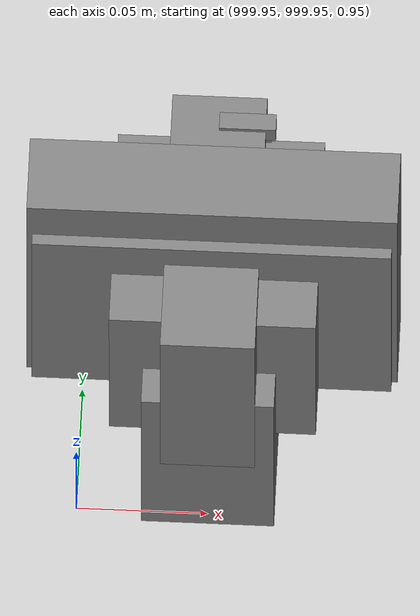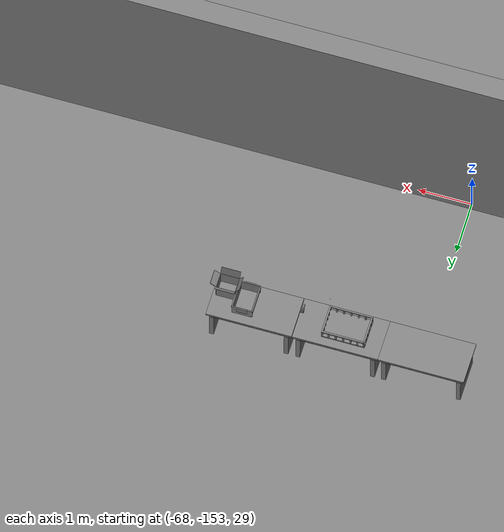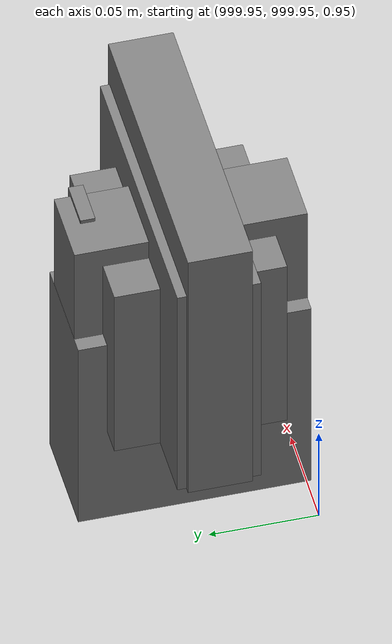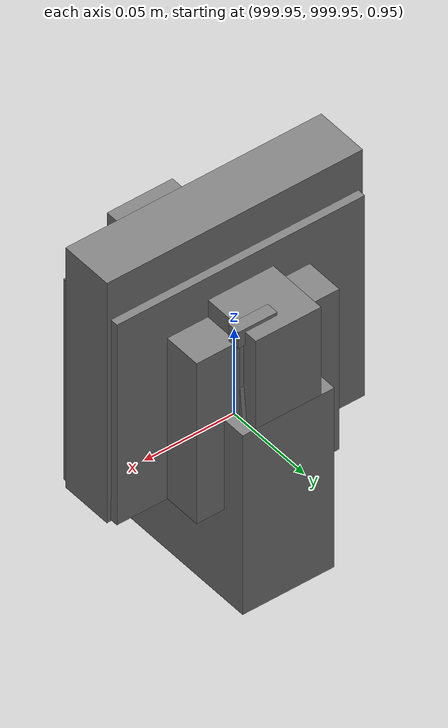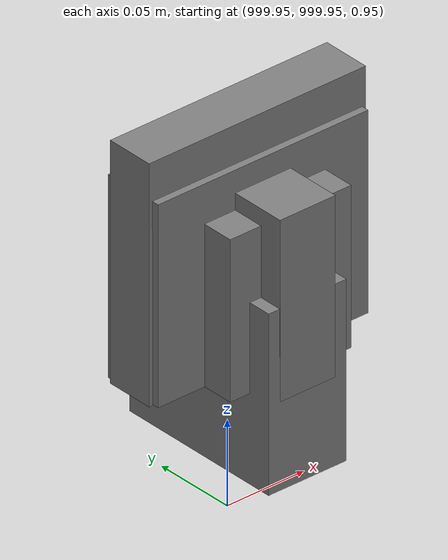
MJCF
<mujoco>
    <option gravity="0.000000000 0.000000000 -9.810000420" timestep="0.0049999999" integrator="implicitfast" density="1.225" viscosity="1.8000001e-05" noslip_iterations="10" iterations="100" sdf_iterations="50">
        <flag multiccd="disable"/>
    </option>
    <size memory="1000M"/>
    <compiler coordinate="local"/>
    <worldbody>
        <light cutoff="30" pos="0 1 1" dir="0 -1 -2"/>
        <light cutoff="30" pos="0 -1 1" dir="0 1 -2"/>
        <body pos="1000.000000000 1000.000000000 1.000000000" euler="0.000000000 0.000000000 180.000000000" name="openloong_gripper_2f85_fix_base_usda_battery_01">
            <geom contype="1" conaffinity="1" density="1000" type="box" material="" rgba="0.500000000 0.500000000 0.500000000 1.000000000" solimp="0.899999976 0.949999988 0.001000000" friction="1.000000000 0.005000000 0.000100000" solref="0.020000000 1.000000000" margin="0" condim="3" group="0" pos="-0.011123657 -0.041940309 0.101691343" quat="1.000000000 0.000000000 0.000000000 0.000000000" size="0.010800000 0.003375000 0.004725000" name="openloong_gripper_2f85_fix_base_usda_geom_7FE1C958_F646_4F02_BEB8_8E0432BC1A42"/>
            <geom contype="1" conaffinity="1" density="1000" type="box" material="" rgba="0.500000000 0.500000000 0.500000000 1.000000000" solimp="0.899999976 0.949999988 0.001000000" friction="1.000000000 0.005000000 0.000100000" solref="0.020000000 1.000000000" margin="0" condim="3" group="0" pos="-0.010876465 -0.044247437 0.047066893" quat="0.998702705 -0.050920475 0.000000000 0.000000000" size="0.009450001 0.002700000 0.024975000" name="openloong_gripper_2f85_fix_base_usda_geom_6335037C_E833_41BB_888D_AD3D01A2E851"/>
            <geom contype="1" conaffinity="1" density="1000" type="box" material="" rgba="0.500000000 0.500000000 0.500000000 1.000000000" solimp="0.899999976 0.949999988 0.001000000" friction="1.000000000 0.005000000 0.000100000" solref="0.020000000 1.000000000" margin="0" condim="3" group="0" pos="-0.001235962 -0.000659180 0.047381196" quat="1.000000000 0.000000000 0.000000000 0.000000000" size="0.039420001 0.039150000 0.047250003" name="openloong_gripper_2f85_fix_base_usda_geom_BD1736EB_0323_4FB0_A75A_7ABF92E8C839"/>
            <geom contype="1" conaffinity="1" density="1000" type="box" material="" rgba="0.500000000 0.500000000 0.500000000 1.000000000" solimp="0.899999976 0.949999988 0.001000000" friction="1.000000000 0.005000000 0.000100000" solref="0.020000000 1.000000000" margin="0" condim="3" group="0" pos="-0.010876465 -0.039138794 0.009851727" quat="1.000000000 0.000000000 0.000000000 0.000000000" size="0.009450001 0.010800000 0.013500000" name="openloong_gripper_2f85_fix_base_usda_geom_27293177_CE43_4650_B5D2_6040F031BA6B"/>
            <geom contype="1" conaffinity="1" density="1000" type="box" material="" rgba="0.500000000 0.500000000 0.500000000 1.000000000" solimp="0.899999976 0.949999988 0.001000000" friction="1.000000000 0.005000000 0.000100000" solref="0.020000000 1.000000000" margin="0" condim="3" group="0" pos="-0.010876465 -0.041528322 0.071508206" quat="1.000000000 0.000000000 0.000000000 0.000000000" size="0.009450001 0.002700000 0.027000001" name="openloong_gripper_2f85_fix_base_usda_geom_89158A8E_63C4_4EFC_8EA3_44964A9332E3"/>
            <freejoint name="openloong_gripper_2f85_fix_base_usda_battery_01_joint"/>
            <site size="0.005000000 0.005000000 0.005000000" rgba="0.500000000 0.500000000 0.500000000 1.000000000" pos="0.000000000 0.000000000 0.000000000" quat="0.999961913 0.008726500 0.000000000 0.000000000" group="0" type="sphere" name="openloong_gripper_2f85_fix_base_usda_battery_01site"/>
        </body>
        <body pos="1000.000000000 999.999938965 1.000000000" euler="0.000000000 0.000000000 180.000000000" name="openloong_gripper_2f85_fix_base_usda_intelcore_i5">
            <geom contype="1" conaffinity="1" density="1000" type="box" material="" rgba="0.500000000 0.500000000 0.500000000 1.000000000" solimp="0.899999976 0.949999988 0.001000000" friction="1.000000000 0.005000000 0.000100000" solref="0.020000000 1.000000000" margin="0" condim="3" group="0" pos="0.000000000 0.000000000 0.051722717" quat="0.707106709 0.000000000 0.000000000 -0.707106769" size="0.052800000 0.018080002 0.052800000" name="openloong_gripper_2f85_fix_base_usda_geom_F170F240_75AB_4DFB_8DC7_181C655E46C0"/>
            <freejoint name="openloong_gripper_2f85_fix_base_usda_intelcore_i5_joint"/>
            <site size="0.005000000 0.005000000 0.005000000" rgba="0.500000000 0.500000000 0.500000000 1.000000000" pos="0.000000000 0.000000000 0.000000000" quat="0.999961913 0.008726534 0.000000000 0.000000000" group="0" type="sphere" name="openloong_gripper_2f85_fix_base_usda_intelcore_i5site"/>
        </body>
        <body pos="-65.801704407 -149.219284058 31.171703339" euler="-33.943470001 -16.136978149 -2.165073156" mocap="true" name="spotlight4_SpotLight"/>
        <body pos="-65.921882629 -149.102996826 31.170383453" euler="-4.921447754 -24.402029037 74.057998657" mocap="true" name="spotlight3_SpotLight"/>
        <body pos="1000.000000000 1000.000000000 1.000000000" euler="0.000000000 0.000000000 180.000000000" name="openloong_gripper_2f85_fix_base_usda_cpu_fan">
            <geom contype="1" conaffinity="1" density="1000" type="box" material="" rgba="0.500000000 0.500000000 0.500000000 1.000000000" solimp="0.899999976 0.949999988 0.001000000" friction="1.000000000 0.005000000 0.000100000" solref="0.020000000 1.000000000" margin="0" condim="3" group="0" pos="0.000000000 0.000000000 0.070034981" quat="0.000000000 0.000000000 0.000000000 1.000000000" size="0.070700005 0.014699999 0.070700005" name="openloong_gripper_2f85_fix_base_usda_geom_7FB9AB22_82E1_4E27_A958_50F9F5C5B8C2"/>
            <freejoint name="openloong_gripper_2f85_fix_base_usda_cpu_fan_joint"/>
            <site size="0.005000000 0.005000000 0.005000000" rgba="0.500000000 0.500000000 0.500000000 1.000000000" pos="0.000000000 0.000000000 0.000000000" quat="0.999961913 0.008726535 0.000000000 0.000000000" group="0" type="sphere" name="openloong_gripper_2f85_fix_base_usda_cpu_fancsite"/>
        </body>
        <body pos="1000.000000000 1000.000000000 1.000000000" euler="0.000000000 0.000000000 180.000000000" name="openloong_gripper_2f85_fix_base_usda_wifi_box">
            <geom contype="1" conaffinity="1" density="1000" type="box" material="" rgba="0.500000000 0.500000000 0.500000000 1.000000000" solimp="0.899999976 0.949999988 0.001000000" friction="1.000000000 0.005000000 0.000100000" solref="0.020000000 1.000000000" margin="0" condim="3" group="0" pos="0.000000000 0.000000000 0.058978677" quat="0.000000000 0.000000047 0.000000000 1.000000000" size="0.068499997 0.018999999 0.059000000" name="openloong_gripper_2f85_fix_base_usda_geom_B146BD96_9B30_4245_A6C4_51BA0E83E9DA"/>
            <freejoint name="openloong_gripper_2f85_fix_base_usda_wifi_box_joint"/>
            <site size="0.005000000 0.005000000 0.005000000" rgba="0.500000000 0.500000000 0.500000000 1.000000000" pos="0.000000000 0.000000000 0.000000000" quat="0.999961913 0.008726500 0.000000000 0.000000000" group="0" type="sphere" name="openloong_gripper_2f85_fix_base_usda_wifi_boxsite"/>
        </body>
        <body pos="1000.000000000 1000.000000000 1.000000000" euler="0.000011953 0.000005123 -179.999984741" name="openloong_gripper_2f85_fix_base_usda_intel_box">
            <geom contype="1" conaffinity="1" density="1000" type="box" material="" rgba="0.500000000 0.500000000 0.500000000 1.000000000" solimp="0.899999976 0.949999988 0.001000000" friction="1.000000000 0.005000000 0.000100000" solref="0.020000000 1.000000000" margin="0" condim="3" group="0" pos="0.000000000 -0.000067139 0.000082284" quat="0.707106709 0.000000225 0.000000253 0.707106650" size="0.052800003 0.025300000 0.052800003" name="openloong_gripper_2f85_fix_base_usda_geom_60D57F3C_35E9_4354_9340_577A19FBC8A7"/>
            <freejoint name="openloong_gripper_2f85_fix_base_usda_intel_box_joint"/>
            <site size="0.005000000 0.005000000 0.005000000" rgba="0.500000000 0.500000000 0.500000000 1.000000000" pos="0.000000000 0.000000000 0.000000000" quat="0.999961913 0.008726500 0.000000000 0.000000000" group="0" type="sphere" name="openloong_gripper_2f85_fix_base_usda_intel_boxsite"/>
        </body>
        <body pos="-66.103446960 -149.135238647 31.164939880" euler="-178.056442261 63.634841919 -161.354171753" mocap="true" name="spotlight2_SpotLight"/>
        <body pos="-64.866622925 -149.383972168 30.183746338" euler="89.999984741 89.999946594 0.000000000" name="openloong_gripper_2f85_fix_base_usda_bluebox_01">
            <geom contype="1" conaffinity="1" density="1000" type="box" material="" rgba="0.500000000 0.500000000 0.500000000 1.000000000" solimp="0.899999976 0.949999988 0.001000000" friction="1.000000000 0.005000000 0.000100000" solref="0.020000000 1.000000000" margin="0" condim="3" group="0" pos="0.276580811 0.187225342 0.000068665" quat="0.707106948 0.000077471 0.707106352 0.000077486" size="0.100000001 0.057999998 0.010000000" name="openloong_gripper_2f85_fix_base_usda_geom_D8073D5B_8385_47B6_80BD_0BFBCB21F3A9"/>
            <geom contype="1" conaffinity="1" density="1000" type="box" material="" rgba="0.500000000 0.500000000 0.500000000 1.000000000" solimp="0.899999976 0.949999988 0.001000000" friction="1.000000000 0.005000000 0.000100000" solref="0.020000000 1.000000000" margin="0" condim="3" group="0" pos="0.000000000 0.002883911 0.000000000" quat="0.999999881 0.000000000 0.000000000 0.000000000" size="0.254000008 0.003000000 0.172000006" name="openloong_gripper_2f85_fix_base_usda_geom_34DDC144_24C3_4899_BED7_693377882F2E"/>
            <geom contype="1" conaffinity="1" density="1000" type="box" material="" rgba="0.500000000 0.500000000 0.500000000 1.000000000" solimp="0.899999976 0.949999988 0.001000000" friction="1.000000000 0.005000000 0.000100000" solref="0.020000000 1.000000000" margin="0" condim="3" group="0" pos="0.000000000 0.124874115 0.173484802" quat="0.999796331 0.020176515 -0.000000015 0.000000030" size="0.259999990 0.119999997 0.007000000" name="openloong_gripper_2f85_fix_base_usda_geom_BB0BFEC0_48E1_48B1_98F9_87ED13C21CB7"/>
            <geom contype="1" conaffinity="1" density="1000" type="box" material="" rgba="0.500000000 0.500000000 0.500000000 1.000000000" solimp="0.899999976 0.949999988 0.001000000" friction="1.000000000 0.005000000 0.000100000" solref="0.020000000 1.000000000" margin="0" condim="3" group="0" pos="0.000000000 0.124874115 -0.173469543" quat="0.999796331 -0.020176545 -0.000000015 0.000000000" size="0.259999990 0.119999997 0.007000000" name="openloong_gripper_2f85_fix_base_usda_geom_ED27BDEA_4E8D_4FC4_9B91_D1FCEDBD7989"/>
            <geom contype="1" conaffinity="1" density="1000" type="box" material="" rgba="0.500000000 0.500000000 0.500000000 1.000000000" solimp="0.899999976 0.949999988 0.001000000" friction="1.000000000 0.005000000 0.000100000" solref="0.020000000 1.000000000" margin="0" condim="3" group="0" pos="0.000000000 0.214008331 0.188980103" quat="0.999912977 0.013176724 0.000000015 0.000000000" size="0.259999990 0.029999999 0.012500000" name="openloong_gripper_2f85_fix_base_usda_geom_83148306_2EF9_4D3E_912E_52B63F9F7161"/>
            <geom contype="1" conaffinity="1" density="1000" type="box" material="" rgba="0.500000000 0.500000000 0.500000000 1.000000000" solimp="0.899999976 0.949999988 0.001000000" friction="1.000000000 0.005000000 0.000100000" solref="0.020000000 1.000000000" margin="0" condim="3" group="0" pos="-0.258361816 0.125289917 0.001876831" quat="0.702796936 -0.020792112 0.710783124 0.020769298" size="0.189999998 0.119999997 0.009000000" name="openloong_gripper_2f85_fix_base_usda_geom_EDDC7CBA_14B2_4235_BA91_244483C75F15"/>
            <geom contype="1" conaffinity="1" density="1000" type="box" material="" rgba="0.500000000 0.500000000 0.500000000 1.000000000" solimp="0.899999976 0.949999988 0.001000000" friction="1.000000000 0.005000000 0.000100000" solref="0.020000000 1.000000000" margin="0" condim="3" group="0" pos="0.000000000 0.214008331 -0.188980103" quat="0.999912977 -0.013176769 0.000000030 0.000000015" size="0.259999990 0.029999999 0.012500000" name="openloong_gripper_2f85_fix_base_usda_geom_FB7C464E_6E23_4F47_B61D_39587D5327CA"/>
            <geom contype="1" conaffinity="1" density="1000" type="box" material="" rgba="0.500000000 0.500000000 0.500000000 1.000000000" solimp="0.899999976 0.949999988 0.001000000" friction="1.000000000 0.005000000 0.000100000" solref="0.020000000 1.000000000" margin="0" condim="3" group="0" pos="-0.276611328 0.187225342 0.000068665" quat="0.707106650 0.000077441 0.707106709 0.000077456" size="0.100000001 0.057999998 0.010000000" name="openloong_gripper_2f85_fix_base_usda_geom_6A592D69_AE7B_44A3_A73A_9FB735A78113"/>
            <geom contype="1" conaffinity="1" density="1000" type="box" material="" rgba="0.500000000 0.500000000 0.500000000 1.000000000" solimp="0.899999976 0.949999988 0.001000000" friction="1.000000000 0.005000000 0.000100000" solref="0.020000000 1.000000000" margin="0" condim="3" group="0" pos="0.258331299 0.125289917 0.001876831" quat="0.702851415 0.018856421 0.710823774 -0.019329369" size="0.189999998 0.119999997 0.009000000" name="openloong_gripper_2f85_fix_base_usda_geom_1F6FD9BB_B1D5_4D4D_8A0B_A8E50B00DCB9"/>
            <freejoint name="openloong_gripper_2f85_fix_base_usda_bluebox_01_joint"/>
            <site size="0.005000000 0.005000000 0.005000000" rgba="0.500000000 0.500000000 0.500000000 1.000000000" pos="0.000000000 0.000000000 0.000000000" quat="0.999961913 0.008726534 0.000000000 0.000000000" group="0" type="sphere" name="openloong_gripper_2f85_fix_base_usda_bluebox_01site"/>
        </body>
        <body pos="-64.496299744 -149.491867065 30.235729218" euler="0.000000000 0.000000000 89.999946594" name="openloong_gripper_2f85_fix_base_usda_cardboardbox_01">
            <geom contype="1" conaffinity="1" density="1000" type="box" material="" rgba="0.500000000 0.500000000 0.500000000 1.000000000" solimp="0.899999976 0.949999988 0.001000000" friction="1.000000000 0.005000000 0.000100000" solref="0.020000000 1.000000000" margin="0" condim="3" group="0" pos="-0.003166199 -0.004086494 0.005052090" quat="1.000000000 0.000000000 0.000000000 0.000000000" size="0.142499998 0.177500010 0.005000000" name="openloong_gripper_2f85_fix_base_usda_geom_50D1D825_05C5_4ABF_B81E_DEE57CCADE32"/>
            <geom contype="1" conaffinity="1" density="1000" type="box" material="" rgba="0.500000000 0.500000000 0.500000000 1.000000000" solimp="0.899999976 0.949999988 0.001000000" friction="1.000000000 0.005000000 0.000100000" solref="0.020000000 1.000000000" margin="0" condim="3" group="0" pos="-0.003166199 0.170316696 0.150570869" quat="1.000000000 0.000000000 0.000000000 0.000000000" size="0.142499998 0.005000000 0.149999991" name="openloong_gripper_2f85_fix_base_usda_geom_8321BE64_9C63_47E4_8D7C_0AA47EE16F69"/>
            <geom contype="1" conaffinity="1" density="1000" type="box" material="" rgba="0.500000000 0.500000000 0.500000000 1.000000000" solimp="0.899999976 0.949999988 0.001000000" friction="1.000000000 0.005000000 0.000100000" solref="0.020000000 1.000000000" margin="0" condim="3" group="0" pos="-0.147399902 -0.005307198 0.150570869" quat="1.000000000 0.000000000 0.000000000 0.000000000" size="0.005000000 0.177500010 0.149999991" name="openloong_gripper_2f85_fix_base_usda_geom_8FC9258B_96A4_48F3_B665_C1D08AFBF17E"/>
            <geom contype="1" conaffinity="1" density="1000" type="box" material="" rgba="0.500000000 0.500000000 0.500000000 1.000000000" solimp="0.899999976 0.949999988 0.001000000" friction="1.000000000 0.005000000 0.000100000" solref="0.020000000 1.000000000" margin="0" condim="3" group="0" pos="0.140275955 -0.005307198 0.150570869" quat="1.000000000 0.000000000 0.000000000 0.000000000" size="0.005000000 0.177500010 0.149999991" name="openloong_gripper_2f85_fix_base_usda_geom_B90C698A_101B_48E8_BC92_99742A2B9037"/>
            <geom contype="1" conaffinity="1" density="1000" type="box" material="" rgba="0.500000000 0.500000000 0.500000000 1.000000000" solimp="0.899999976 0.949999988 0.001000000" friction="1.000000000 0.005000000 0.000100000" solref="0.020000000 1.000000000" margin="0" condim="3" group="0" pos="-0.003166199 -0.181550980 0.150570869" quat="1.000000000 0.000000000 0.000000000 0.000000000" size="0.142499998 0.005000000 0.149999991" name="openloong_gripper_2f85_fix_base_usda_geom_8B7F7788_70FC_4E2F_938C_B9670A45449D"/>
            <freejoint name="openloong_gripper_2f85_fix_base_usda_cardboardbox_01_joint"/>
            <site size="0.005000000 0.005000000 0.005000000" rgba="0.500000000 0.500000000 0.500000000 1.000000000" pos="0.000000000 0.000000000 0.000000000" quat="0.999961913 0.008726535 0.000000000 0.000000000" group="0" type="sphere" name="openloong_gripper_2f85_fix_base_usda_site_20670F19_A337_4818_8582_F259394B1017"/>
            <body pos="0.139160156 -0.004048347 0.301930904" euler="-179.999954224 49.383502960 179.999954224" name="openloong_gripper_2f85_fix_base_usda_A1_006">
                <geom contype="1" conaffinity="1" density="1000" type="box" material="" rgba="0.500000000 0.500000000 0.500000000 1.000000000" solimp="0.899999976 0.949999988 0.001000000" friction="1.000000000 0.005000000 0.000100000" solref="0.020000000 1.000000000" margin="0" condim="3" group="0" pos="-0.071587563 0.000009537 0.001745224" quat="0.999999881 0.000000000 0.000000000 0.000000000" size="0.071249999 0.179999992 0.002500000" name="openloong_gripper_2f85_fix_base_usda_geom_936B8809_6C70_40AE_AE6A_C7FC2AAE6CA8"/>
                <joint armature="0" stiffness="0.07" damping="0.0099999998" axis="0.000000 1.000000 0.000000" type="hinge" name="openloong_gripper_2f85_fix_base_usda_A1_006"/>
            </body>
            <body pos="-0.145902634 -0.004086494 0.301938057" euler="-180.000000000 -60.000011444 -180.000000000" name="openloong_gripper_2f85_fix_base_usda_A2_006">
                <geom contype="1" conaffinity="1" density="1000" type="box" material="" rgba="0.500000000 0.500000000 0.500000000 1.000000000" solimp="0.899999976 0.949999988 0.001000000" friction="1.000000000 0.005000000 0.000100000" solref="0.020000000 1.000000000" margin="0" condim="3" group="0" pos="0.071268082 0.000009537 0.002717972" quat="0.000002921 0.000000000 -0.000000030 0.999999881" size="0.071249999 0.179999992 0.002500000" name="openloong_gripper_2f85_fix_base_usda_geom_7461DE24_DD51_4696_985D_8FE4EC034586"/>
                <joint armature="0" stiffness="0.07" damping="0.0099999998" axis="0.000000 1.000000 0.000000" type="hinge" name="openloong_gripper_2f85_fix_base_usda_A2_006"/>
            </body>
            <body pos="-0.003385544 0.175991058 0.301930904" euler="-125.858116150 -0.000004561 0.000002331" name="openloong_gripper_2f85_fix_base_usda_B2_006">
                <geom contype="1" conaffinity="1" density="1000" type="box" material="" rgba="0.500000000 0.500000000 0.500000000 1.000000000" solimp="0.899999976 0.949999988 0.001000000" friction="1.000000000 0.005000000 0.000100000" solref="0.020000000 1.000000000" margin="0" condim="3" group="0" pos="0.000009537 -0.070939064 -0.002470016" quat="0.999614120 0.027776197 -0.000000015 0.000000030" size="0.137500003 0.064999998 0.005000000" name="openloong_gripper_2f85_fix_base_usda_geom_2D5122F8_C1F6_4121_8549_D5B22B0E2D61"/>
                <joint armature="0" stiffness="0.07" damping="0.0099999998" axis="1.000000 0.000000 0.000000" type="hinge" name="openloong_gripper_2f85_fix_base_usda_B2_006"/>
            </body>
            <body pos="-0.003385544 -0.184140205 0.301938057" euler="147.805557251 0.000000000 0.000000000" name="openloong_gripper_2f85_fix_base_usda_B1_006">
                <geom contype="1" conaffinity="1" density="1000" type="box" material="" rgba="0.500000000 0.500000000 0.500000000 1.000000000" solimp="0.899999976 0.949999988 0.001000000" friction="1.000000000 0.005000000 0.000100000" solref="0.020000000 1.000000000" margin="0" condim="3" group="0" pos="-0.000028610 0.070202351 -0.002703667" quat="0.999614179 -0.027776167 0.000000000 0.000000000" size="0.137500003 0.064999998 0.005000000" name="openloong_gripper_2f85_fix_base_usda_geom_93C6F1AA_1A8A_4C61_977C_348434F97EAB"/>
                <joint armature="0" stiffness="0.07" damping="0.0099999998" axis="1.000000 0.000000 0.000000" type="hinge" name="openloong_gripper_2f85_fix_base_usda_B1_006"/>
            </body>
        </body>
        <body pos="-65.882858276 -149.481979370 30.229999542" euler="-64.487716675 0.000000000 0.000000000" name="openloong_gripper_2f85_fix_base_usda_Barcode">
            <geom contype="1" conaffinity="1" density="1000" type="box" material="" rgba="0.500000000 0.500000000 0.500000000 1.000000000" solimp="0.899999976 0.949999988 0.001000000" friction="1.000000000 0.005000000 0.000100000" solref="0.020000000 1.000000000" margin="0" condim="3" group="0" pos="0.000000000 0.013038635 0.001419067" quat="0.000000000 0.000000000 0.000000000 1.000000119" size="0.034000002 0.010000000 0.017999999" name="openloong_gripper_2f85_fix_base_usda_geom_CE9AC429_7B54_4E39_B0B7_DBCBC7BEDEF3"/>
            <geom contype="1" conaffinity="1" density="1000" type="box" material="" rgba="0.500000000 0.500000000 0.500000000 1.000000000" solimp="0.899999976 0.949999988 0.001000000" friction="1.000000000 0.005000000 0.000100000" solref="0.020000000 1.000000000" margin="0" condim="3" group="0" pos="0.000000000 -0.035301208 -0.007095337" quat="0.000000000 0.000000000 -0.043619365 0.999048233" size="0.028999999 0.010000000 0.020000000" name="openloong_gripper_2f85_fix_base_usda_geom_79AE1AA5_42D6_4377_92FD_09C00F7A4279"/>
            <geom contype="1" conaffinity="1" density="1000" type="box" material="" rgba="0.500000000 0.500000000 0.500000000 1.000000000" solimp="0.899999976 0.949999988 0.001000000" friction="1.000000000 0.005000000 0.000100000" solref="0.020000000 1.000000000" margin="0" condim="3" group="0" pos="0.000000000 -0.043411255 -0.011749268" quat="0.922262907 0.386563420 0.000000000 0.000000000" size="0.026000001 0.010000000 0.020000000" name="openloong_gripper_2f85_fix_base_usda_geom_E94BCB32_2575_4316_8F2A_C973F537D4F0"/>
            <geom contype="1" conaffinity="1" density="1000" type="box" material="" rgba="0.500000000 0.500000000 0.500000000 1.000000000" solimp="0.899999976 0.949999988 0.001000000" friction="1.000000000 0.005000000 0.000100000" solref="0.020000000 1.000000000" margin="0" condim="3" group="0" pos="0.000000000 -0.016967773 -0.031860352" quat="0.000000000 0.000000000 0.000000000 1.000000119" size="0.008000000 0.010000000 0.013000000" name="openloong_gripper_2f85_fix_base_usda_geom_13AC2D21_60C0_44D7_BFA5_FBD08A3F6B66"/>
            <geom contype="1" conaffinity="1" density="1000" type="box" material="" rgba="0.500000000 0.500000000 0.500000000 1.000000000" solimp="0.899999976 0.949999988 0.001000000" friction="1.000000000 0.005000000 0.000100000" solref="0.020000000 1.000000000" margin="0" condim="3" group="0" pos="0.000000000 -0.001869202 0.000312805" quat="0.953716993 0.300705761 0.000000000 0.000000000" size="0.032000002 0.010000000 0.018999999" name="openloong_gripper_2f85_fix_base_usda_geom_D2FDDC8D_C684_41E0_9B59_D25F637B1FC4"/>
            <geom contype="1" conaffinity="1" density="1000" type="box" material="" rgba="0.500000000 0.500000000 0.500000000 1.000000000" solimp="0.899999976 0.949999988 0.001000000" friction="1.000000000 0.005000000 0.000100000" solref="0.020000000 1.000000000" margin="0" condim="3" group="0" pos="0.000000000 -0.019531250 -0.003173828" quat="0.953716993 0.300705761 0.000000000 0.000000000" size="0.030999999 0.010000000 0.020000000" name="openloong_gripper_2f85_fix_base_usda_geom_7910E968_1138_4272_9916_F5DC1D4B1D1A"/>
            <geom contype="1" conaffinity="1" density="1000" type="box" material="" rgba="0.500000000 0.500000000 0.500000000 1.000000000" solimp="0.899999976 0.949999988 0.001000000" friction="1.000000000 0.005000000 0.000100000" solref="0.020000000 1.000000000" margin="0" condim="3" group="0" pos="0.000000000 -0.035301208 -0.007095337" quat="0.953716993 0.300705761 0.000000000 0.000000000" size="0.028999999 0.010000000 0.020000000" name="openloong_gripper_2f85_fix_base_usda_geom_7E6450E6_B511_4A35_97C9_C64D3B1BD89F"/>
            <geom contype="1" conaffinity="1" density="1000" type="box" material="" rgba="0.500000000 0.500000000 0.500000000 1.000000000" solimp="0.899999976 0.949999988 0.001000000" friction="1.000000000 0.005000000 0.000100000" solref="0.020000000 1.000000000" margin="0" condim="3" group="0" pos="0.000000000 -0.042617798 -0.071121216" quat="0.000000000 0.000000000 0.000000000 1.000000119" size="0.013000000 0.021000000 0.059999999" name="openloong_gripper_2f85_fix_base_usda_geom_E60019A2_8062_4FD2_A157_ACD0B09E34BE"/>
            <freejoint name="openloong_gripper_2f85_fix_base_usda_Barcode_joint"/>
            <site size="0.005000000 0.005000000 0.005000000" rgba="0.500000000 0.500000000 0.500000000 1.000000000" pos="0.000000000 0.000000000 0.000000000" quat="1.000000000 0.000000000 0.000000000 0.000000000" group="0" type="sphere" name="openloong_gripper_2f85_fix_base_usda_Barcode_site"/>
        </body>
        <body pos="-66.745018005 -149.392349243 30.184000015" euler="0.000000000 0.000000000 89.999946594" name="[22333075718972]_Basket_01">
            <geom contype="1" conaffinity="1" density="1000" type="box" material="" rgba="0.500000000 0.500000000 0.500000000 1.000000000" solimp="0.899999976 0.949999988 0.001000000" friction="1.000000000 0.005000000 0.000100000" solref="0.020000000 1.000000000" margin="0" condim="3" group="0" pos="-0.052425385 0.389207840 0.089787483" quat="0.707107008 0.000000000 0.000000000 0.707106411" size="0.014249999 0.014249999 0.059999999" name="[22333075718972]_geom_A721E010_221E_4255_8B04_1A0FBB180DE5"/>
            <geom contype="1" conaffinity="1" density="1000" type="box" material="" rgba="0.500000000 0.500000000 0.500000000 1.000000000" solimp="0.899999976 0.949999988 0.001000000" friction="1.000000000 0.005000000 0.000100000" solref="0.020000000 1.000000000" margin="0" condim="3" group="0" pos="0.264015198 -0.133043289 0.089787483" quat="0.707107008 0.000000000 0.000000000 0.707106411" size="0.014249999 0.014249999 0.059999999" name="[22333075718972]_geom_A5B2CBFA_6D8D_4E48_918B_032A18A27C92"/>
            <geom contype="1" conaffinity="1" density="1000" type="box" material="" rgba="0.500000000 0.500000000 0.500000000 1.000000000" solimp="0.899999976 0.949999988 0.001000000" friction="1.000000000 0.005000000 0.000100000" solref="0.020000000 1.000000000" margin="0" condim="3" group="0" pos="-0.264015198 -0.265548706 0.089793205" quat="0.707107008 0.000000000 0.000000000 0.707106411" size="0.014249999 0.014249999 0.059999999" name="[22333075718972]_geom_A12EECA8_1757_4E9C_AAB9_BCC8CD2CA7C3"/>
            <geom contype="1" conaffinity="1" density="1000" type="box" material="" rgba="0.500000000 0.500000000 0.500000000 1.000000000" solimp="0.899999976 0.949999988 0.001000000" friction="1.000000000 0.005000000 0.000100000" solref="0.020000000 1.000000000" margin="0" condim="3" group="0" pos="-0.160263062 -0.389322281 0.089793205" quat="0.707107008 0.000000000 0.000000000 0.707106411" size="0.014249999 0.014249999 0.059999999" name="[22333075718972]_geom_AF994AB9_7D92_48FB_89F5_4CA49BDDDF5D"/>
            <geom contype="1" conaffinity="1" density="1000" type="box" material="" rgba="0.500000000 0.500000000 0.500000000 1.000000000" solimp="0.899999976 0.949999988 0.001000000" friction="1.000000000 0.005000000 0.000100000" solref="0.020000000 1.000000000" margin="0" condim="3" group="0" pos="0.162265778 -0.389322281 0.089787483" quat="0.707107008 0.000000000 0.000000000 0.707106411" size="0.014249999 0.014249999 0.059999999" name="[22333075718972]_geom_F755566A_40A6_4199_80C5_CA25AA4D40A9"/>
            <geom contype="1" conaffinity="1" density="1000" type="box" material="" rgba="0.500000000 0.500000000 0.500000000 1.000000000" solimp="0.899999976 0.949999988 0.001000000" friction="1.000000000 0.005000000 0.000100000" solref="0.020000000 1.000000000" margin="0" condim="3" group="0" pos="0.264015198 0.389207840 0.089787483" quat="0.707107008 0.000000000 0.000000000 0.707106411" size="0.014249999 0.014249999 0.059999999" name="[22333075718972]_geom_D47AFF8F_348E_409A_BA3D_E89F51361B5C"/>
            <geom contype="1" conaffinity="1" density="1000" type="box" material="" rgba="0.500000000 0.500000000 0.500000000 1.000000000" solimp="0.899999976 0.949999988 0.001000000" friction="1.000000000 0.005000000 0.000100000" solref="0.020000000 1.000000000" margin="0" condim="3" group="0" pos="-0.264015198 -0.133043289 0.089793205" quat="0.707107008 0.000000000 0.000000000 0.707106411" size="0.014249999 0.014249999 0.059999999" name="[22333075718972]_geom_1B199236_6CC7_47B1_A2C6_0A0490EB9ECF"/>
            <geom contype="1" conaffinity="1" density="1000" type="box" material="" rgba="0.500000000 0.500000000 0.500000000 1.000000000" solimp="0.899999976 0.949999988 0.001000000" friction="1.000000000 0.005000000 0.000100000" solref="0.020000000 1.000000000" margin="0" condim="3" group="0" pos="-0.264026642 0.269256592 0.089793205" quat="0.707107008 0.000000000 0.000000000 0.707106411" size="0.014249999 0.014249999 0.059999999" name="[22333075718972]_geom_CFD9E424_F96D_46E7_957B_F68FC1E5D650"/>
            <geom contype="1" conaffinity="1" density="1000" type="box" material="" rgba="0.500000000 0.500000000 0.500000000 1.000000000" solimp="0.899999976 0.949999988 0.001000000" friction="1.000000000 0.005000000 0.000100000" solref="0.020000000 1.000000000" margin="0" condim="3" group="0" pos="0.054462433 0.389207840 0.089787483" quat="0.707107008 0.000000000 0.000000000 0.707106411" size="0.014249999 0.014249999 0.059999999" name="[22333075718972]_geom_926155D4_6CB3_47AF_9046_96EFF5B32380"/>
            <geom contype="1" conaffinity="1" density="1000" type="box" material="" rgba="0.500000000 0.500000000 0.500000000 1.000000000" solimp="0.899999976 0.949999988 0.001000000" friction="1.000000000 0.005000000 0.000100000" solref="0.020000000 1.000000000" margin="0" condim="3" group="0" pos="0.054462433 -0.389322281 0.089787483" quat="0.707107008 0.000000000 0.000000000 0.707106411" size="0.014249999 0.014249999 0.059999999" name="[22333075718972]_geom_5BE1828C_9EEC_4945_8ECB_F47D1CFBCC66"/>
            <geom contype="1" conaffinity="1" density="1000" type="box" material="" rgba="0.500000000 0.500000000 0.500000000 1.000000000" solimp="0.899999976 0.949999988 0.001000000" friction="1.000000000 0.005000000 0.000100000" solref="0.020000000 1.000000000" margin="0" condim="3" group="0" pos="0.264015198 0.269256592 0.089793205" quat="0.707107008 0.000000000 0.000000000 0.707106411" size="0.014249999 0.014249999 0.059999999" name="[22333075718972]_geom_893B132B_9625_4543_BA3E_BFF63EF14ABB"/>
            <geom contype="1" conaffinity="1" density="1000" type="box" material="" rgba="0.500000000 0.500000000 0.500000000 1.000000000" solimp="0.899999976 0.949999988 0.001000000" friction="1.000000000 0.005000000 0.000100000" solref="0.020000000 1.000000000" margin="0" condim="3" group="0" pos="0.264015198 -0.389322281 0.089787483" quat="0.707107008 0.000000000 0.000000000 0.707106411" size="0.014249999 0.014249999 0.059999999" name="[22333075718972]_geom_749803FA_D3BC_43B2_BD38_1E0A45536210"/>
            <geom contype="1" conaffinity="1" density="1000" type="box" material="" rgba="0.500000000 0.500000000 0.500000000 1.000000000" solimp="0.899999976 0.949999988 0.001000000" friction="1.000000000 0.005000000 0.000100000" solref="0.020000000 1.000000000" margin="0" condim="3" group="0" pos="0.000000000 0.000000000 0.015998840" quat="0.707107008 0.000000000 0.000000000 0.707106411" size="0.403499991 0.279000014 0.015750000" name="[22333075718972]_geom_D5ADB1CB_E358_46E8_888C_41D635B7A721"/>
            <geom contype="1" conaffinity="1" density="1000" type="box" material="" rgba="0.500000000 0.500000000 0.500000000 1.000000000" solimp="0.899999976 0.949999988 0.001000000" friction="1.000000000 0.005000000 0.000100000" solref="0.020000000 1.000000000" margin="0" condim="3" group="0" pos="0.000000000 -0.389476776 0.163619041" quat="0.707107008 0.000000000 0.000000000 0.707106411" size="0.015000000 0.277500004 0.015750000" name="[22333075718972]_geom_75BD98A7_F364_4D4C_9ACE_0E9EDBE180B7"/>
            <geom contype="1" conaffinity="1" density="1000" type="box" material="" rgba="0.500000000 0.500000000 0.500000000 1.000000000" solimp="0.899999976 0.949999988 0.001000000" friction="1.000000000 0.005000000 0.000100000" solref="0.020000000 1.000000000" margin="0" condim="3" group="0" pos="0.162265778 0.389207840 0.089787483" quat="0.707107008 0.000000000 0.000000000 0.707106411" size="0.014249999 0.014249999 0.059999999" name="[22333075718972]_geom_E922EF00_0B01_4A37_A7D3_D1B730D58D95"/>
            <geom contype="1" conaffinity="1" density="1000" type="box" material="" rgba="0.500000000 0.500000000 0.500000000 1.000000000" solimp="0.899999976 0.949999988 0.001000000" friction="1.000000000 0.005000000 0.000100000" solref="0.020000000 1.000000000" margin="0" condim="3" group="0" pos="0.000000000 0.389471054 0.163619041" quat="0.707107008 0.000000000 0.000000000 0.707106411" size="0.015000000 0.277500004 0.015750000" name="[22333075718972]_geom_B3E40BE4_1C89_4862_8342_C2D1227B999B"/>
            <geom contype="1" conaffinity="1" density="1000" type="box" material="" rgba="0.500000000 0.500000000 0.500000000 1.000000000" solimp="0.899999976 0.949999988 0.001000000" friction="1.000000000 0.005000000 0.000100000" solref="0.020000000 1.000000000" margin="0" condim="3" group="0" pos="-0.263511658 0.000000000 0.163619041" quat="0.707107008 0.000000000 0.000000000 0.707106411" size="0.403499991 0.015000000 0.015750000" name="[22333075718972]_geom_A16947D6_B921_4E4E_AA75_7D940172729C"/>
            <geom contype="1" conaffinity="1" density="1000" type="box" material="" rgba="0.500000000 0.500000000 0.500000000 1.000000000" solimp="0.899999976 0.949999988 0.001000000" friction="1.000000000 0.005000000 0.000100000" solref="0.020000000 1.000000000" margin="0" condim="3" group="0" pos="-0.264015198 0.141334534 0.089793205" quat="0.707107008 0.000000000 0.000000000 0.707106411" size="0.014249999 0.014249999 0.059999999" name="[22333075718972]_geom_1B169381_2825_4DA3_AEAC_76BCFBBEBDFC"/>
            <geom contype="1" conaffinity="1" density="1000" type="box" material="" rgba="0.500000000 0.500000000 0.500000000 1.000000000" solimp="0.899999976 0.949999988 0.001000000" friction="1.000000000 0.005000000 0.000100000" solref="0.020000000 1.000000000" margin="0" condim="3" group="0" pos="0.264015198 -0.265548706 0.089787483" quat="0.707107008 0.000000000 0.000000000 0.707106411" size="0.014249999 0.014249999 0.059999999" name="[22333075718972]_geom_D88D8E3B_403E_44DE_BEA4_77A40141F85D"/>
            <geom contype="1" conaffinity="1" density="1000" type="box" material="" rgba="0.500000000 0.500000000 0.500000000 1.000000000" solimp="0.899999976 0.949999988 0.001000000" friction="1.000000000 0.005000000 0.000100000" solref="0.020000000 1.000000000" margin="0" condim="3" group="0" pos="-0.160263062 0.389207840 0.089787483" quat="0.707107008 0.000000000 0.000000000 0.707106411" size="0.014249999 0.014249999 0.059999999" name="[22333075718972]_geom_FA4D424C_97C0_4D49_A748_46CD87F42B33"/>
            <geom contype="1" conaffinity="1" density="1000" type="box" material="" rgba="0.500000000 0.500000000 0.500000000 1.000000000" solimp="0.899999976 0.949999988 0.001000000" friction="1.000000000 0.005000000 0.000100000" solref="0.020000000 1.000000000" margin="0" condim="3" group="0" pos="-0.052425385 -0.389322281 0.089787483" quat="0.707107008 0.000000000 0.000000000 0.707106411" size="0.014249999 0.014249999 0.059999999" name="[22333075718972]_geom_18786472_27E9_4D66_8DAF_7645648E33A9"/>
            <geom contype="1" conaffinity="1" density="1000" type="box" material="" rgba="0.500000000 0.500000000 0.500000000 1.000000000" solimp="0.899999976 0.949999988 0.001000000" friction="1.000000000 0.005000000 0.000100000" solref="0.020000000 1.000000000" margin="0" condim="3" group="0" pos="-0.264026642 -0.389322281 0.089793205" quat="0.707107008 0.000000000 0.000000000 0.707106411" size="0.014249999 0.014249999 0.059999999" name="[22333075718972]_geom_CD618F5D_8BBC_4996_BE90_B0480AB149D4"/>
            <geom contype="1" conaffinity="1" density="1000" type="box" material="" rgba="0.500000000 0.500000000 0.500000000 1.000000000" solimp="0.899999976 0.949999988 0.001000000" friction="1.000000000 0.005000000 0.000100000" solref="0.020000000 1.000000000" margin="0" condim="3" group="0" pos="0.264015198 0.141334534 0.089787483" quat="0.707107008 0.000000000 0.000000000 0.707106411" size="0.014249999 0.014249999 0.059999999" name="[22333075718972]_geom_5C11C90B_8EDB_453D_AB7A_0367B4EB667E"/>
            <geom contype="1" conaffinity="1" density="1000" type="box" material="" rgba="0.500000000 0.500000000 0.500000000 1.000000000" solimp="0.899999976 0.949999988 0.001000000" friction="1.000000000 0.005000000 0.000100000" solref="0.020000000 1.000000000" margin="0" condim="3" group="0" pos="-0.264015198 0.389207840 0.089793205" quat="0.707107008 0.000000000 0.000000000 0.707106411" size="0.014249999 0.014249999 0.059999999" name="[22333075718972]_geom_4F126511_2AC7_432F_82DE_929D29FF59F6"/>
            <geom contype="1" conaffinity="1" density="1000" type="box" material="" rgba="0.500000000 0.500000000 0.500000000 1.000000000" solimp="0.899999976 0.949999988 0.001000000" friction="1.000000000 0.005000000 0.000100000" solref="0.020000000 1.000000000" margin="0" condim="3" group="0" pos="0.264015198 0.004480362 0.089787483" quat="0.707107008 0.000000000 0.000000000 0.707106411" size="0.014249999 0.014249999 0.059999999" name="[22333075718972]_geom_CD548053_2CE1_492E_A770_E4F629322014"/>
            <geom contype="1" conaffinity="1" density="1000" type="box" material="" rgba="0.500000000 0.500000000 0.500000000 1.000000000" solimp="0.899999976 0.949999988 0.001000000" friction="1.000000000 0.005000000 0.000100000" solref="0.020000000 1.000000000" margin="0" condim="3" group="0" pos="0.263694763 -0.000011444 0.163619041" quat="0.707107008 0.000000000 0.000000000 0.707106411" size="0.403499991 0.015000000 0.015750000" name="[22333075718972]_geom_C9706B59_2F4D_4B53_BCB2_8EE51A37AD05"/>
            <geom contype="1" conaffinity="1" density="1000" type="box" material="" rgba="0.500000000 0.500000000 0.500000000 1.000000000" solimp="0.899999976 0.949999988 0.001000000" friction="1.000000000 0.005000000 0.000100000" solref="0.020000000 1.000000000" margin="0" condim="3" group="0" pos="-0.264015198 0.004480362 0.089793205" quat="0.707107008 0.000000000 0.000000000 0.707106411" size="0.014249999 0.014249999 0.059999999" name="[22333075718972]_geom_5F15C744_4768_44A5_AD6D_A9151DA79F56"/>
            <freejoint name="[22333075718972]_joint_69E73569_EDAA_437F_A9D2_8DB10A018A17"/>
        </body>
        <body pos="0.000000000 0.000000000 0.000000000" euler="0.000000000 0.000000000 0.000000000" name="Static Objects_Static Objects">
            <geom contype="1" conaffinity="1" density="1000" type="box" material="" rgba="0.500000000 0.500000000 0.500000000 1.000000000" solimp="0.899999976 0.949999988 0.001000000" friction="1.000000000 0.005000000 0.000100000" solref="0.020000000 1.000000000" margin="0" condim="3" group="0" pos="-67.544113159 -149.365814209 29.727830887" quat="0.500000417 0.499999970 0.499999553 0.499999970" size="0.381000012 0.319999993 0.041000001" name="Static Objects_geom_FA5A9FD4_D354_4531_A19B_8F75B6768973"/>
            <geom contype="1" conaffinity="1" density="1000" type="box" material="" rgba="0.500000000 0.500000000 0.500000000 1.000000000" solimp="0.899999976 0.949999988 0.001000000" friction="1.000000000 0.005000000 0.000100000" solref="0.020000000 1.000000000" margin="0" condim="3" group="0" pos="-68.239501953 -149.365814209 30.086868286" quat="0.500000417 0.499999970 0.499999553 0.499999970" size="0.370999992 0.039500002 0.745000005" name="Static Objects_geom_624EF938_7E6C_44BC_A2C8_A2C479BD0465"/>
            <geom contype="1" conaffinity="1" density="1000" type="box" material="" rgba="0.500000000 0.500000000 0.500000000 1.000000000" solimp="0.899999976 0.949999988 0.001000000" friction="1.000000000 0.005000000 0.000100000" solref="0.020000000 1.000000000" margin="0" condim="3" group="0" pos="-68.239501953 -149.365814209 30.147235870" quat="0.500000417 0.499999970 0.499999553 0.499999970" size="0.400000006 0.022000000 0.800000012" name="Static Objects_geom_5BBDB727_7A49_4E30_B1AA_CEB484AB4203"/>
            <geom contype="1" conaffinity="1" density="1000" type="box" material="" rgba="0.500000000 0.500000000 0.500000000 1.000000000" solimp="0.899999976 0.949999988 0.001000000" friction="1.000000000 0.005000000 0.000100000" solref="0.020000000 1.000000000" margin="0" condim="3" group="0" pos="-68.934890747 -149.365814209 29.727830887" quat="0.500000417 0.499999970 0.499999553 0.499999970" size="0.381000012 0.319999993 0.041000001" name="Static Objects_geom_1A9EF5C8_E4A5_4FAB_B541_49FECDE36D48"/>
            <geom contype="1" conaffinity="1" density="1000" type="box" material="" rgba="0.500000000 0.500000000 0.500000000 1.000000000" solimp="0.899999976 0.949999988 0.001000000" friction="1.000000000 0.005000000 0.000100000" solref="0.020000000 1.000000000" margin="0" condim="3" group="0" pos="-68.239501953 -149.365814209 29.561563492" quat="0.500000417 0.499999970 0.499999553 0.499999970" size="0.020000000 0.022000000 0.660000026" name="Static Objects_geom_8FBAA6C2_1E7B_4891_8E6E_4A7D07B1007C"/>
            <geom contype="1" conaffinity="1" density="1000" type="box" material="" rgba="0.500000000 0.500000000 0.500000000 1.000000000" solimp="0.899999976 0.949999988 0.001000000" friction="1.000000000 0.005000000 0.000100000" solref="0.020000000 1.000000000" margin="0" condim="3" group="0" pos="-65.945671082 -149.365814209 29.727830887" quat="0.500000417 0.499999970 0.499999553 0.499999970" size="0.381000012 0.319999993 0.041000001" name="Static Objects_geom_84CA8836_9650_43E2_8CBA_18B0DB7BBED2"/>
            <geom contype="1" conaffinity="1" density="1000" type="box" material="" rgba="0.500000000 0.500000000 0.500000000 1.000000000" solimp="0.899999976 0.949999988 0.001000000" friction="1.000000000 0.005000000 0.000100000" solref="0.020000000 1.000000000" margin="0" condim="3" group="0" pos="-66.641059875 -149.365814209 30.086868286" quat="0.500000417 0.499999970 0.499999553 0.499999970" size="0.370999992 0.039500002 0.745000005" name="Static Objects_geom_ECCC0293_F273_49CB_BCE3_42E7B911C489"/>
            <geom contype="1" conaffinity="1" density="1000" type="box" material="" rgba="0.500000000 0.500000000 0.500000000 1.000000000" solimp="0.899999976 0.949999988 0.001000000" friction="1.000000000 0.005000000 0.000100000" solref="0.020000000 1.000000000" margin="0" condim="3" group="0" pos="-66.641059875 -149.365814209 30.147235870" quat="0.500000417 0.499999970 0.499999553 0.499999970" size="0.400000006 0.022000000 0.800000012" name="Static Objects_geom_14C10249_18D5_4DE5_B5C3_637CDABFC49C"/>
            <geom contype="1" conaffinity="1" density="1000" type="box" material="" rgba="0.500000000 0.500000000 0.500000000 1.000000000" solimp="0.899999976 0.949999988 0.001000000" friction="1.000000000 0.005000000 0.000100000" solref="0.020000000 1.000000000" margin="0" condim="3" group="0" pos="-67.336448669 -149.365814209 29.727830887" quat="0.500000417 0.499999970 0.499999553 0.499999970" size="0.381000012 0.319999993 0.041000001" name="Static Objects_geom_D1D12C76_772B_4F5C_8B53_2F62C1BC21AD"/>
            <geom contype="1" conaffinity="1" density="1000" type="box" material="" rgba="0.500000000 0.500000000 0.500000000 1.000000000" solimp="0.899999976 0.949999988 0.001000000" friction="1.000000000 0.005000000 0.000100000" solref="0.020000000 1.000000000" margin="0" condim="3" group="0" pos="-66.641059875 -149.365814209 29.561563492" quat="0.500000417 0.499999970 0.499999553 0.499999970" size="0.020000000 0.022000000 0.660000026" name="Static Objects_geom_5274E2A0_48D4_42C4_8EEE_98390109091C"/>
            <geom contype="1" conaffinity="1" density="1000" type="box" material="" rgba="0.500000000 0.500000000 0.500000000 1.000000000" solimp="0.899999976 0.949999988 0.001000000" friction="1.000000000 0.005000000 0.000100000" solref="0.020000000 1.000000000" margin="0" condim="3" group="0" pos="-64.338577271 -149.365814209 29.727830887" quat="0.500000417 0.499999970 0.499999553 0.499999970" size="0.381000012 0.319999993 0.041000001" name="Static Objects_geom_E0783B99_D138_4B94_BB10_0DE30DFC6370"/>
            <geom contype="1" conaffinity="1" density="1000" type="box" material="" rgba="0.500000000 0.500000000 0.500000000 1.000000000" solimp="0.899999976 0.949999988 0.001000000" friction="1.000000000 0.005000000 0.000100000" solref="0.020000000 1.000000000" margin="0" condim="3" group="0" pos="-65.033966064 -149.365814209 30.086868286" quat="0.500000417 0.499999970 0.499999553 0.499999970" size="0.370999992 0.039500002 0.745000005" name="Static Objects_geom_687C61D9_1C3E_4515_BDE7_6942875CA21B"/>
            <geom contype="1" conaffinity="1" density="1000" type="box" material="" rgba="0.500000000 0.500000000 0.500000000 1.000000000" solimp="0.899999976 0.949999988 0.001000000" friction="1.000000000 0.005000000 0.000100000" solref="0.020000000 1.000000000" margin="0" condim="3" group="0" pos="-65.033966064 -149.365814209 30.147235870" quat="0.500000417 0.499999970 0.499999553 0.499999970" size="0.400000006 0.022000000 0.800000012" name="Static Objects_geom_F8EA91DA_B164_4347_954B_BD6F0C853CB7"/>
            <geom contype="1" conaffinity="1" density="1000" type="box" material="" rgba="0.500000000 0.500000000 0.500000000 1.000000000" solimp="0.899999976 0.949999988 0.001000000" friction="1.000000000 0.005000000 0.000100000" solref="0.020000000 1.000000000" margin="0" condim="3" group="0" pos="-65.729354858 -149.365814209 29.727830887" quat="0.500000417 0.499999970 0.499999553 0.499999970" size="0.381000012 0.319999993 0.041000001" name="Static Objects_geom_AC878948_648B_4995_A8D8_301A5BDD4F15"/>
            <geom contype="1" conaffinity="1" density="1000" type="box" material="" rgba="0.500000000 0.500000000 0.500000000 1.000000000" solimp="0.899999976 0.949999988 0.001000000" friction="1.000000000 0.005000000 0.000100000" solref="0.020000000 1.000000000" margin="0" condim="3" group="0" pos="-65.033966064 -149.365814209 29.561563492" quat="0.500000417 0.499999970 0.499999553 0.499999970" size="0.020000000 0.022000000 0.660000026" name="Static Objects_geom_8F8739DF_0763_4C82_8053_4921FA320858"/>
            <geom contype="1" conaffinity="1" density="1000" type="box" material="" rgba="0.500000000 0.500000000 0.500000000 1.000000000" solimp="0.899999976 0.949999988 0.001000000" friction="1.000000000 0.005000000 0.000100000" solref="0.020000000 1.000000000" margin="0" condim="3" group="0" pos="-61.754566193 -137.853729248 33.906845093" quat="0.707107067 0.000000000 0.000000000 0.707106471" size="0.759999990 0.759999990 4.500000000" name="Static Objects_geom_45ACB831_A828_4702_88A3_4A916E0F4959"/>
            <geom contype="1" conaffinity="1" density="1000" type="box" material="" rgba="0.500000000 0.500000000 0.500000000 1.000000000" solimp="0.899999976 0.949999988 0.001000000" friction="1.000000000 0.005000000 0.000100000" solref="0.020000000 1.000000000" margin="0" condim="3" group="0" pos="-57.511135101 -144.927108765 31.707921982" quat="1.000000000 0.000000000 0.000000000 0.000000000" size="0.200000003 8.000000000 2.299999952" name="Static Objects_geom_6DFC32FD_D049_4F5D_BB73_5AC9C1694CBC"/>
            <geom contype="1" conaffinity="1" density="1000" type="box" material="" rgba="0.500000000 0.500000000 0.500000000 1.000000000" solimp="0.899999976 0.949999988 0.001000000" friction="1.000000000 0.005000000 0.000100000" solref="0.020000000 1.000000000" margin="0" condim="3" group="0" pos="-80.517646790 -157.574050903 31.688196182" quat="0.707107067 0.000000000 0.000000000 0.707106471" size="0.600000024 0.600000024 2.299999952" name="Static Objects_geom_840CF606_98C2_4782_92A5_DAA1CDC2B229"/>
            <geom contype="1" conaffinity="1" density="1000" type="box" material="" rgba="0.500000000 0.500000000 0.500000000 1.000000000" solimp="0.899999976 0.949999988 0.001000000" friction="1.000000000 0.005000000 0.000100000" solref="0.020000000 1.000000000" margin="0" condim="3" group="0" pos="-80.711044312 -147.414932251 31.666158676" quat="1.000000000 0.000000000 0.000000000 0.000000000" size="0.200000003 10.000000000 2.299999952" name="Static Objects_geom_B7269D42_8852_45B3_9EAA_6FC66FE0E39A"/>
            <geom contype="1" conaffinity="1" density="1000" type="box" material="" rgba="0.500000000 0.500000000 0.500000000 1.000000000" solimp="0.899999976 0.949999988 0.001000000" friction="1.000000000 0.005000000 0.000100000" solref="0.020000000 1.000000000" margin="0" condim="3" group="0" pos="-57.687217712 -137.434692383 31.688196182" quat="0.707107067 0.000000000 0.000000000 0.707106471" size="0.600000024 0.600000024 2.299999952" name="Static Objects_geom_4149C1BC_E6B0_47DC_975F_9F972BA166F1"/>
            <geom contype="1" conaffinity="1" density="1000" type="box" material="" rgba="0.500000000 0.500000000 0.500000000 1.000000000" solimp="0.899999976 0.949999988 0.001000000" friction="1.000000000 0.005000000 0.000100000" solref="0.020000000 1.000000000" margin="0" condim="3" group="0" pos="-69.537033081 -140.263229370 31.714921951" quat="0.707107067 0.000000000 0.000000000 0.707106471" size="0.759999990 4.500000000 2.299999952" name="Static Objects_geom_6ADD6C1B_77F1_4ACD_BE65_8AD0225F20F1"/>
            <geom contype="1" conaffinity="1" density="1000" type="box" material="" rgba="0.500000000 0.500000000 0.500000000 1.000000000" solimp="0.899999976 0.949999988 0.001000000" friction="1.000000000 0.005000000 0.000100000" solref="0.020000000 1.000000000" margin="0" condim="3" group="0" pos="-80.073638916 -137.853713989 33.906845093" quat="0.707107067 0.000000000 0.000000000 0.707106471" size="0.759999990 0.759999990 4.500000000" name="Static Objects_geom_88DB19D4_5D35_4057_9E2C_F9B1FDB33112"/>
            <geom contype="1" conaffinity="1" density="1000" type="box" material="" rgba="0.500000000 0.500000000 0.500000000 1.000000000" solimp="0.899999976 0.949999988 0.001000000" friction="1.000000000 0.005000000 0.000100000" solref="0.020000000 1.000000000" margin="0" condim="3" group="0" pos="-73.406707764 -155.734664917 31.707921982" quat="1.000000000 0.000000000 0.000000000 0.000000000" size="0.200000003 3.000000000 2.299999952" name="Static Objects_geom_69148472_E727_4C10_B738_DBAEB1C5D740"/>
            <geom contype="1" conaffinity="1" density="1000" type="box" material="" rgba="0.500000000 0.500000000 0.500000000 1.000000000" solimp="0.899999976 0.949999988 0.001000000" friction="1.000000000 0.005000000 0.000100000" solref="0.020000000 1.000000000" margin="0" condim="3" group="0" pos="-68.497543335 -137.448257446 31.707921982" quat="0.707107067 0.000000000 0.000000000 0.707106471" size="0.200000003 14.000000000 2.299999952" name="Static Objects_geom_79E6F4A6_02EB_4640_8864_2F01AEB71369"/>
            <geom contype="1" conaffinity="1" density="1000" type="cylinder" material="" rgba="0.500000000 0.500000000 0.500000000 1.000000000" solimp="0.899999976 0.949999988 0.001000000" friction="1.000000000 0.005000000 0.000100000" solref="0.020000000 1.000000000" margin="0" condim="3" group="0" pos="-68.868522644 -142.134506226 31.711090088" quat="0.707107067 0.000000000 0.000000000 0.707106471" size="0.509999990 2.299999952 1.000000000" name="Static Objects_geom_AD4B00A2_CE91_40D9_AF4A_E7B8BAB01A98"/>
            <geom contype="1" conaffinity="1" density="1000" type="plane" material="" rgba="0.500000000 0.500000000 0.500000000 1.000000000" solimp="0.899999976 0.949999988 0.001000000" friction="1.000000000 0.005000000 0.000100000" solref="0.020000000 1.000000000" margin="0" condim="3" group="0" pos="-72.873703003 -147.131927490 29.409669876" quat="1.000000000 0.000000000 0.000000000 0.000000000" size="18.000000000 14.000000000 1.000000000" name="Static Objects_geom_5F9FBECF_FD23_47CD_A68F_814D6A4C290D"/>
            <geom contype="1" conaffinity="1" density="1000" type="box" material="" rgba="0.500000000 0.500000000 0.500000000 1.000000000" solimp="0.899999976 0.949999988 0.001000000" friction="1.000000000 0.005000000 0.000100000" solref="0.020000000 1.000000000" margin="0" condim="3" group="0" pos="-79.943580627 -157.782272339 31.707921982" quat="0.707107067 0.000000000 0.000000000 0.707106471" size="0.200000003 7.000000000 2.299999952" name="Static Objects_geom_E22D5C0C_95BC_4E09_BD26_42B2681614D9"/>
            <geom contype="1" conaffinity="1" density="1000" type="box" material="" rgba="0.500000000 0.500000000 0.500000000 1.000000000" solimp="0.899999976 0.949999988 0.001000000" friction="1.000000000 0.005000000 0.000100000" solref="0.020000000 1.000000000" margin="0" condim="3" group="0" pos="-65.421028137 -152.903442383 31.707921982" quat="0.707107067 0.000000000 0.000000000 0.707106471" size="0.200000003 7.800000191 2.299999952" name="Static Objects_geom_E104D2FC_F4B8_45ED_930D_D40D4B680811"/>
            <geom contype="1" conaffinity="1" density="1000" type="box" material="" rgba="0.500000000 0.500000000 0.500000000 1.000000000" solimp="0.899999976 0.949999988 0.001000000" friction="1.000000000 0.005000000 0.000100000" solref="0.020000000 1.000000000" margin="0" condim="3" group="0" pos="-74.776908875 -149.964416504 31.688196182" quat="1.000000000 0.000000000 0.000000000 0.000000000" size="0.600000024 0.409999996 2.299999952" name="Static Objects_geom_43F67725_8F4F_487C_94EB_9D6B43776FCD"/>
            <geom contype="1" conaffinity="1" density="1000" type="cylinder" material="" rgba="0.500000000 0.500000000 0.500000000 1.000000000" solimp="0.899999976 0.949999988 0.001000000" friction="1.000000000 0.005000000 0.000100000" solref="0.020000000 1.000000000" margin="0" condim="3" group="0" pos="-60.161884308 -142.134506226 31.711090088" quat="0.707107067 0.000000000 0.000000000 0.707106471" size="0.509999990 2.299999952 1.000000000" name="Static Objects_geom_213691AF_7586_42B5_AD57_67638E8958BD"/>
            <geom contype="1" conaffinity="1" density="1000" type="cylinder" material="" rgba="0.500000000 0.500000000 0.500000000 1.000000000" solimp="0.899999976 0.949999988 0.001000000" friction="1.000000000 0.005000000 0.000100000" solref="0.020000000 1.000000000" margin="0" condim="3" group="0" pos="-75.382453918 -149.963455200 31.711090088" quat="0.707107067 0.000000000 0.000000000 0.707106471" size="0.409999996 2.299999952 1.000000000" name="Static Objects_geom_E99BFA3B_1F12_4639_8794_E9381809A1C3"/>
            <geom contype="1" conaffinity="1" density="1000" type="cylinder" material="" rgba="0.500000000 0.500000000 0.500000000 1.000000000" solimp="0.899999976 0.949999988 0.001000000" friction="1.000000000 0.005000000 0.000100000" solref="0.020000000 1.000000000" margin="0" condim="3" group="0" pos="-74.154960632 -149.963455200 31.711090088" quat="0.707107067 0.000000000 0.000000000 0.707106471" size="0.409999996 2.299999952 1.000000000" name="Static Objects_geom_BF9B3EA2_8CE1_4040_90A4_D187E8481DAB"/>
            <geom contype="1" conaffinity="1" density="1000" type="cylinder" material="" rgba="0.500000000 0.500000000 0.500000000 1.000000000" solimp="0.899999976 0.949999988 0.001000000" friction="1.000000000 0.005000000 0.000100000" solref="0.020000000 1.000000000" margin="0" condim="3" group="0" pos="-77.566612244 -142.134506226 31.711090088" quat="0.707107067 0.000000000 0.000000000 0.707106471" size="0.509999990 2.299999952 1.000000000" name="Static Objects_geom_A4B6C2FB_D5FE_4525_9DC4_F37A0BC288C0"/>
        </body>
        <body pos="-66.291030884 -149.869689941 29.018842697" euler="0.000000000 0.000000000 89.999946594" mocap="true" name="openloong_gripper_2f85_fix_base_usda_leftHandMocap"/>
        <body pos="-66.291030884 -149.869689941 29.018842697" euler="0.000000000 0.000000000 89.999946594" mocap="true" name="openloong_gripper_2f85_fix_base_usda_rightHandMocap"/>
        <body pos="-66.291030884 -149.869689941 30.218843460" euler="0.000000000 0.000000000 89.999946594" name="openloong_gripper_2f85_fix_base_usda_base_link">
            <geom contype="1" conaffinity="1" density="1000" type="mesh" material="" rgba="0.783999979 0.783999979 0.783999979 1.000000000" solimp="0.899999976 0.949999988 0.001000000" friction="1.000000000 0.005000000 0.000100000" solref="0.020000000 1.000000000" margin="0" condim="3" group="3" mesh="base_link" pos="0.000000000 0.000000000 0.000000000" quat="1.000000000 0.000000000 0.000000000 0.000000000" size="1.000000000 1.000000000 1.000000000" name="openloong_gripper_2f85_fix_base_usda__geom_7_139D0BAD_DEE3_4C4D_B303_26A0CC117685"/>
            <site size="0.005000000 0.005000000 0.005000000" rgba="0.500000000 0.500000000 0.500000000 1.000000000" pos="0.000000000 0.000000000 0.000000000" quat="1.000000000 0.000000000 0.000000000 0.000000000" group="0" type="sphere" name="openloong_gripper_2f85_fix_base_usda_imu"/>
            <inertial mass="22.447001" pos="-0.005664100 -0.001336700 0.238289997" diaginertia="0.374352545 0.277180195 0.220617250" quat="0.999247074 0.035235517 -0.015086859 0.006023135"/>
            <body pos="0.000000000 0.000000000 0.299997330" euler="0.000000000 0.000000000 0.000000000" name="openloong_gripper_2f85_fix_base_usda_dummy_body">
                <geom contype="1" conaffinity="1" density="1000" type="sphere" material="" rgba="0.783999979 0.783999979 0.783999979 1.000000000" solimp="0.899999976 0.949999988 0.001000000" friction="1.000000000 0.005000000 0.000100000" solref="0.020000000 1.000000000" margin="0" condim="3" group="3" pos="0.000000000 0.000000000 0.000000000" quat="1.000000000 0.000000000 0.000000000 0.000000000" size="0.010000000 0.000000000 0.000000000" name="openloong_gripper_2f85_fix_base_usda__geom_8_B9814559_CECC_4B21_8CE6_862EBE9B5A4C"/>
                <joint armature="0.0099999998" stiffness="0" damping="0.1" axis="0.000000 0.000000 1.000000" type="hinge" name="openloong_gripper_2f85_fix_base_usda_dummy_joint"/>
                <site size="0.010000000 0.005000000 0.005000000" rgba="0.500000000 0.500000000 0.500000000 1.000000000" pos="0.000000000 0.000000000 0.000000000" quat="1.000000000 0.000000000 0.000000000 0.000000000" group="3" type="sphere" name="openloong_gripper_2f85_fix_base_usda_dummy_site"/>
            </body>
            <body pos="0.009002686 0.000000000 0.406400681" euler="0.000000000 0.000000000 0.000000000" name="openloong_gripper_2f85_fix_base_usda_Link_head_yaw">
                <geom contype="1" conaffinity="1" density="1000" type="mesh" material="" rgba="0.783999979 0.783999979 0.783999979 1.000000000" solimp="0.899999976 0.949999988 0.001000000" friction="1.000000000 0.005000000 0.000100000" solref="0.020000000 1.000000000" margin="0" condim="3" group="3" mesh="Link_head_yaw" pos="0.000000000 0.000000000 0.000000000" quat="1.000000000 0.000000000 0.000000000 0.000000000" size="1.000000000 1.000000000 1.000000000" name="openloong_gripper_2f85_fix_base_usda__geom_10_468A5194_8CBC_4EFE_958C_9AE5BDCC0018"/>
                <inertial mass="0.84249002" pos="0.000000000 -0.002081400 0.044801001" diaginertia="0.000700588 0.000629000 0.000553812" quat="0.706933022 -0.015675601 0.015677100 0.706933022"/>
                <body pos="0.000000000 -0.034599304 0.048500061" euler="0.000000000 0.000000000 0.000000000" name="openloong_gripper_2f85_fix_base_usda_Link_head_pitch">
                    <geom contype="1" conaffinity="1" density="1000" type="mesh" material="" rgba="0.783999979 0.783999979 0.783999979 1.000000000" solimp="0.899999976 0.949999988 0.001000000" friction="1.000000000 0.005000000 0.000100000" solref="0.020000000 1.000000000" margin="0" condim="3" group="3" mesh="Link_head_pitch" pos="0.000000000 0.000000000 0.000000000" quat="1.000000000 0.000000000 0.000000000 0.000000000" size="1.000000000 1.000000000 1.000000000" name="openloong_gripper_2f85_fix_base_usda__geom_12_468AE6F4_7A02_4AF0_B07B_84D8B6EC83CC"/>
                    <inertial mass="1.3943" pos="0.020569000 0.033004001 0.125000000" diaginertia="0.006381400 0.006289940 0.004481460" quat="0.973390222 0.008406822 0.228157058 0.019624906"/>
                    <body pos="0.000000000 0.029998779 0.000000000" euler="0.000000000 0.000000000 0.000000000" name="openloong_gripper_2f85_fix_base_usda_neck_center_body">
                        <site size="0.010000000 0.005000000 0.005000000" rgba="0.500000000 0.500000000 0.500000000 1.000000000" pos="0.000000000 0.000000000 0.000000000" quat="1.000000000 0.000000000 0.000000000 0.000000000" group="3" type="sphere" name="openloong_gripper_2f85_fix_base_usda_neck_center_site"/>
                        <body pos="0.020004272 0.000000000 0.149999619" euler="-0.000002229 39.998176575 -90.000205994" name="openloong_gripper_2f85_fix_base_usda_camera_head">
                            <site size="0.010000000 0.005000000 0.005000000" rgba="0.500000000 0.500000000 0.500000000 1.000000000" pos="0.000000000 0.000000000 0.000000000" quat="1.000000000 0.000000000 0.000000000 0.000000000" group="3" type="sphere" name="openloong_gripper_2f85_fix_base_usda_camera_head_site"/>
                        </body>
                    </body>
                </body>
            </body>
            <body pos="0.003997803 -0.161598206 0.392200470" euler="0.000000000 0.000000000 0.000000000" name="openloong_gripper_2f85_fix_base_usda_Link_arm_r_01">
                <geom contype="1" conaffinity="1" density="1000" type="mesh" material="" rgba="0.783999979 0.783999979 0.783999979 1.000000000" solimp="0.899999976 0.949999988 0.001000000" friction="1.000000000 0.005000000 0.000100000" solref="0.020000000 1.000000000" margin="0" condim="3" group="3" mesh="Link_arm_r_01" pos="0.000000000 0.000000000 0.000000000" quat="1.000000000 0.000000000 0.000000000 0.000000000" size="1.000000000 1.000000000 1.000000000" name="openloong_gripper_2f85_fix_base_usda__geom_14_E089FCA5_E126_4AEF_B535_0BD1F0240517"/>
                <joint armature="0.0099999998" stiffness="0" damping="1" axis="0.000000 -1.000000 0.000000" limited="true" range="-170.000015259 170.000015259" type="hinge" name="openloong_gripper_2f85_fix_base_usda_J_arm_r_01"/>
                <inertial mass="0.75641" pos="0.004494600 -0.038293999 -0.000001874" diaginertia="0.000842990 0.000803050 0.000587120" quat="-0.000163502 0.707098067 0.000812463 0.707115054"/>
                <body pos="-0.041992188 -0.041000366 0.000000000" euler="0.000000000 0.000000000 0.000000000" name="openloong_gripper_2f85_fix_base_usda_Link_arm_r_02">
                    <geom contype="1" conaffinity="1" density="1000" type="mesh" material="" rgba="0.783999979 0.783999979 0.783999979 1.000000000" solimp="0.899999976 0.949999988 0.001000000" friction="1.000000000 0.005000000 0.000100000" solref="0.020000000 1.000000000" margin="0" condim="3" group="3" mesh="Link_arm_r_02" pos="0.000000000 0.000000000 0.000000000" quat="1.000000000 0.000000000 0.000000000 0.000000000" size="1.000000000 1.000000000 1.000000000" name="openloong_gripper_2f85_fix_base_usda__geom_16_BE40C169_B65B_4E0C_BCF0_1768D8762208"/>
                    <joint armature="0.0099999998" stiffness="0" damping="1" axis="-1.000000 0.000000 0.000000" limited="true" range="-105.000244141 105.000244141" type="hinge" name="openloong_gripper_2f85_fix_base_usda_J_arm_r_02"/>
                    <inertial mass="0.98500001" pos="0.041999999 -0.067430697 0.000000000" diaginertia="0.002262690 0.001730990 0.001154020" quat="0.500000000 0.500000000 -0.500000000 0.500000000"/>
                    <body pos="0.041992188 -0.122596741 0.000000000" euler="0.000000000 0.000000000 0.000000000" name="openloong_gripper_2f85_fix_base_usda_Link_arm_r_03">
                        <geom contype="1" conaffinity="1" density="1000" type="mesh" material="" rgba="0.783999979 0.783999979 0.783999979 1.000000000" solimp="0.899999976 0.949999988 0.001000000" friction="1.000000000 0.005000000 0.000100000" solref="0.020000000 1.000000000" margin="0" condim="3" group="3" mesh="Link_arm_r_03" pos="0.000000000 0.000000000 0.000000000" quat="1.000000000 0.000000000 0.000000000 0.000000000" size="1.000000000 1.000000000 1.000000000" name="openloong_gripper_2f85_fix_base_usda__geom_18_131FAFB4_FBBA_4495_A721_3E6D32FF39F2"/>
                        <joint armature="0.0099999998" stiffness="0" damping="1" axis="0.000000 -1.000000 0.000000" limited="true" range="-170.000015259 170.000015259" type="hinge" name="openloong_gripper_2f85_fix_base_usda_J_arm_r_03"/>
                        <inertial mass="0.95899999" pos="-0.001413580 -0.164663002 0.020757901" diaginertia="0.002101340 0.002064590 0.000754802" quat="0.560480952 0.454391927 -0.443732947 0.531497955"/>
                        <body pos="0.035293579 -0.177406311 0.023998260" euler="0.000000000 0.000000000 0.000000000" name="openloong_gripper_2f85_fix_base_usda_Link_arm_r_04">
                            <geom contype="1" conaffinity="1" density="1000" type="mesh" material="" rgba="0.783999979 0.783999979 0.783999979 1.000000000" solimp="0.899999976 0.949999988 0.001000000" friction="1.000000000 0.005000000 0.000100000" solref="0.020000000 1.000000000" margin="0" condim="3" group="3" mesh="Link_arm_r_04" pos="0.000000000 0.000000000 0.000000000" quat="1.000000000 0.000000000 0.000000000 0.000000000" size="1.000000000 1.000000000 1.000000000" name="openloong_gripper_2f85_fix_base_usda__geom_20_7BED1A94_B6D7_4AD8_BC9D_1C4617A595A7"/>
                            <joint armature="0.0099999998" stiffness="0" damping="1" axis="-1.000000 0.000000 0.000000" limited="true" range="0.000000000 170.000015259" type="hinge" name="openloong_gripper_2f85_fix_base_usda_J_arm_r_04"/>
                            <inertial mass="0.60000002" pos="-0.038727000 -0.060766999 -0.021003000" diaginertia="0.001092610 0.000712422 0.000645102" quat="0.327701002 0.632602990 -0.467366993 0.523443997"/>
                            <body pos="-0.035293579 -0.103492737 -0.023998260" euler="0.000000000 0.000000000 0.000000000" name="openloong_gripper_2f85_fix_base_usda_Link_arm_r_05">
                                <geom contype="1" conaffinity="1" density="1000" type="mesh" material="" rgba="0.783999979 0.783999979 0.783999979 1.000000000" solimp="0.899999976 0.949999988 0.001000000" friction="1.000000000 0.005000000 0.000100000" solref="0.020000000 1.000000000" margin="0" condim="3" group="3" mesh="Link_arm_r_05" pos="0.000000000 0.000000000 0.000000000" quat="1.000000000 0.000000000 0.000000000 0.000000000" size="1.000000000 1.000000000 1.000000000" name="openloong_gripper_2f85_fix_base_usda__geom_22_F50F81C8_A6C9_4B70_A2B5_46EA39FCA006"/>
                                <joint armature="0.0099999998" stiffness="0" damping="1" axis="0.000000 -1.000000 0.000000" limited="true" range="-170.000015259 170.000015259" type="hinge" name="openloong_gripper_2f85_fix_base_usda_J_arm_r_05"/>
                                <inertial mass="0.68976003" pos="0.000032712 -0.068658002 -0.000111780" diaginertia="0.002522510 0.002411100 0.000448695" quat="0.707660973 0.706543028 -0.002603360 0.002470550"/>
                                <body pos="-0.026489258 -0.196502686 0.000000000" euler="0.000000000 0.000000000 0.000000000" name="openloong_gripper_2f85_fix_base_usda_Link_arm_r_06">
                                    <geom contype="1" conaffinity="1" density="1000" type="mesh" material="" rgba="0.783999979 0.783999979 0.783999979 1.000000000" solimp="0.899999976 0.949999988 0.001000000" friction="1.000000000 0.005000000 0.000100000" solref="0.020000000 1.000000000" margin="0" condim="3" group="3" mesh="Link_arm_r_06" pos="0.000000000 0.000000000 0.000000000" quat="1.000000000 0.000000000 0.000000000 0.000000000" size="1.000000000 1.000000000 1.000000000" name="openloong_gripper_2f85_fix_base_usda__geom_24_7C16D738_B354_4D6E_82ED_AEE86E067EB7"/>
                                    <joint armature="0.0099999998" stiffness="0" damping="1" axis="1.000000 0.000000 0.000000" limited="true" range="-105.000244141 105.000244141" type="hinge" name="openloong_gripper_2f85_fix_base_usda_J_arm_r_06"/>
                                    <inertial mass="0.28" pos="0.026078001 -0.000000896 0.001663700" diaginertia="0.000156930 0.000145601 0.000104979" quat="0.707080841 0.001851080 0.001883810 0.707127810"/>
                                    <body pos="0.026489258 0.000000000 0.031799316" euler="0.000000000 0.000000000 0.000000000" name="openloong_gripper_2f85_fix_base_usda_Link_arm_r_07">
                                        <geom contype="1" conaffinity="1" density="1000" type="mesh" material="" rgba="0.783999979 0.783999979 0.783999979 1.000000000" solimp="0.899999976 0.949999988 0.001000000" friction="1.000000000 0.005000000 0.000100000" solref="0.020000000 1.000000000" margin="0" condim="3" group="3" mesh="Link_arm_r_07" pos="0.000000000 0.000000000 0.000000000" quat="1.000000000 0.000000000 0.000000000 0.000000000" size="1.000000000 1.000000000 1.000000000" name="openloong_gripper_2f85_fix_base_usda__geom_26_359B0748_9A45_462F_9F48_E71CF868154D"/>
                                        <joint armature="0.0099999998" stiffness="0" damping="1" axis="0.000000 0.000000 1.000000" limited="true" range="-60.000133514 60.000133514" type="hinge" name="openloong_gripper_2f85_fix_base_usda_J_arm_r_07"/>
                                        <inertial mass="0.61353999" pos="-0.007859000 -0.158170000 -0.027736001" diaginertia="0.003037610 0.002570910 0.000729379" quat="0.427542925 0.443532884 -0.553093910 0.560867906"/>
                                        <body pos="0.000000000 0.286994934 -0.270000458" euler="150.000350952 -0.000001649 -0.000000442" name="openloong_gripper_2f85_fix_base_usda_camera_wrist_r">
                                            <site size="0.010000000 0.005000000 0.005000000" rgba="0.500000000 0.500000000 0.500000000 1.000000000" pos="0.000000000 0.000000000 0.000000000" quat="1.000000000 0.000000000 0.000000000 0.000000000" group="3" type="sphere" name="openloong_gripper_2f85_fix_base_usda_camera_wrist_r_site"/>
                                        </body>
                                        <body pos="0.000000000 -0.220008850 -0.033002853" euler="0.000000000 0.000000000 179.999969482" name="openloong_gripper_2f85_fix_base_usda_ee_center_body_r">
                                            <site size="0.010000000 0.005000000 0.005000000" rgba="0.500000000 0.500000000 0.500000000 1.000000000" pos="0.000000000 0.000000000 0.000000000" quat="1.000000000 0.000000000 0.000000000 0.000000000" group="3" type="sphere" name="openloong_gripper_2f85_fix_base_usda_ee_center_site_r"/>
                                        </body>
                                        <body pos="0.000000000 -0.066001892 -0.031000137" euler="89.999984741 0.000000000 180.000000000" name="openloong_gripper_2f85_fix_base_usda_zbr_base_link">
                                            <geom contype="1" conaffinity="1" density="1000" type="mesh" material="" rgba="0.783999979 0.783999979 0.783999979 1.000000000" solimp="0.899999976 0.949999988 0.001000000" friction="1.000000000 0.005000000 0.000100000" solref="0.020000000 1.000000000" margin="0" condim="3" group="3" mesh="base" pos="0.000000000 0.000003815 -0.000007629" quat="1.000000000 0.000000000 0.000000000 0.000000000" size="1.000000238 1.000000238 1.000000238" name="openloong_gripper_2f85_fix_base_usda__geom_30_443466E7_5069_48F4_B91F_7C8B4857F48B"/>
                                            <inertial mass="0.77744102" pos="0.000000000 -0.000027039 0.035467502" diaginertia="0.000260285 0.000225381 0.000152708" quat="0.999998808 -0.001528488 0.000000000 0.000000000"/>
                                            <body pos="-0.030609138 0.004745484 0.065696731" euler="-89.999984741 -0.000000000 0.000000000" name="openloong_gripper_2f85_fix_base_usda_r_left_driver">
                                                <geom contype="1" conaffinity="1" density="1000" type="mesh" material="" rgba="0.783999979 0.783999979 0.783999979 1.000000000" solimp="0.899999976 0.949999988 0.001000000" friction="1.000000000 0.005000000 0.000100000" solref="0.020000000 1.000000000" margin="0" condim="3" group="3" mesh="driver" pos="0.030609138 0.054901138 -0.004699708" quat="0.707106829 0.707106709 0.000000000 -0.000000000" size="1.000000238 1.000000238 1.000000238" name="openloong_gripper_2f85_fix_base_usda__geom_32_2025D0AC_7832_48C7_B765_F9BF692FA960"/>
                                                <joint armature="0.0049999999" stiffness="0" damping="0.1" axis="0.000000 0.000000 1.000000" limited="true" range="0.000000000 51.566200256" type="hinge" name="openloong_gripper_2f85_fix_base_usda_r_left_driver_joint"/>
                                                <inertial mass="0.0089956298" pos="0.000000000 0.017754700 0.001073140" diaginertia="0.000001724 0.000001609 0.000000322" quat="0.681301236 0.732003212 0.000000000 0.000000000"/>
                                                <body pos="-0.031402595 0.004524232 -0.010200503" euler="0.000000000 0.000000000 180.000000000" name="openloong_gripper_2f85_fix_base_usda_r_left_coupler">
                                                    <geom contype="1" conaffinity="1" density="1000" type="mesh" material="" rgba="0.783999979 0.783999979 0.783999979 1.000000000" solimp="0.899999976 0.949999988 0.001000000" friction="1.000000000 0.005000000 0.000100000" solref="0.020000000 1.000000000" margin="0" condim="3" group="3" mesh="coupler" pos="-0.062011734 -0.050354015 0.005500795" quat="0.707106829 -0.707106709 0.000000000 -0.000000000" size="1.000000238 1.000000238 1.000000238" name="openloong_gripper_2f85_fix_base_usda__geom_34_3A38D256_E656_48BB_9227_513DD4D8EBF2"/>
                                                    <inertial mass="0.0140974" pos="0.000000000 0.003012090 0.023217499" diaginertia="0.000004162 0.000003522 0.000000888" quat="0.705635548 -0.045590367 0.045590367 0.705635548"/>
                                                </body>
                                            </body>
                                            <body pos="-0.012695315 -0.012001040 0.072212234" euler="-89.999984741 -0.000000000 0.000000000" name="openloong_gripper_2f85_fix_base_usda_r_left_spring_link">
                                                <geom contype="1" conaffinity="1" density="1000" type="mesh" material="" rgba="0.783999979 0.783999979 0.783999979 1.000000000" solimp="0.899999976 0.949999988 0.001000000" friction="1.000000000 0.005000000 0.000100000" solref="0.020000000 1.000000000" margin="0" condim="3" group="3" mesh="spring_link" pos="0.012695315 0.061416641 0.012050631" quat="0.707106829 0.707106709 0.000000000 -0.000000000" size="1.000000238 1.000000238 1.000000238" name="openloong_gripper_2f85_fix_base_usda__geom_36_087F784D_420B_4F55_A84D_EB15B937CDB2"/>
                                                <joint armature="0.001" stiffness="0.050000001" damping="0.00125" axis="0.000000 0.000000 1.000000" limited="true" range="-17.000000000 51.566200256" type="hinge" name="openloong_gripper_2f85_fix_base_usda_r_left_spring_link_joint"/>
                                                <inertial mass="0.0221642" pos="-0.000000009 0.018162400 0.021265799" diaginertia="0.000008969 0.000006717 0.000002639" quat="0.663403213 -0.244737089 0.244737089 0.663403213"/>
                                                <body pos="-0.038208015 -0.042503368 0.002950669" euler="180.000000000 0.000000000 -0.002185660" name="openloong_gripper_2f85_fix_base_usda_r_left_follower">
                                                    <geom contype="1" conaffinity="1" density="1000" type="mesh" material="" rgba="0.783999979 0.783999979 0.783999979 1.000000000" solimp="0.899999976 0.949999988 0.001000000" friction="1.000000000 0.005000000 0.000100000" solref="0.020000000 1.000000000" margin="0" condim="3" group="3" mesh="tongue" pos="0.050918590 -0.103920005 -0.009099962" quat="0.707106829 -0.707106709 0.000000030 0.000000030" size="1.000000238 1.000000238 1.000000238" name="openloong_gripper_2f85_fix_base_usda__geom_40_A0125F18_9B98_4689_A3DD_76B25EDBE704"/>
                                                    <geom contype="1" conaffinity="1" density="1000" type="mesh" material="" rgba="0.783999979 0.783999979 0.783999979 1.000000000" solimp="0.899999976 0.949999988 0.001000000" friction="1.000000000 0.005000000 0.000100000" solref="0.020000000 1.000000000" margin="0" condim="3" group="3" mesh="follower" pos="0.050918590 -0.103920005 -0.009099962" quat="0.707106829 -0.707106709 0.000000030 0.000000030" size="1.000000238 1.000000238 1.000000238" name="openloong_gripper_2f85_fix_base_usda__geom_39_B2AEBAD5_44C4_4F9F_B20E_9AA5B5351BC8"/>
                                                    <joint armature="0.001" stiffness="0" damping="0.1" axis="0.000000 0.000000 1.000000" limited="true" range="-49.999961853 51.566200256" type="hinge" name="openloong_gripper_2f85_fix_base_usda_r_left_follower"/>
                                                    <inertial mass="0.0125222" pos="0.000000000 -0.011046000 0.012478600" diaginertia="0.000002674 0.000002456 0.000000602" quat="0.986436546 0.164143041 0.000000000 0.000000000"/>
                                                    <body pos="-0.037765510 -0.103912376 -0.009099962" euler="-89.999984741 0.000000000 0.000004829" name="openloong_gripper_2f85_fix_base_usda_r_left_pad">
                                                        <geom contype="1" conaffinity="1" density="1000" type="box" material="" rgba="0.550000012 0.550000012 0.550000012 1.000000000" solimp="0.949999988 0.990000010 0.001000000" friction="0.699999988 0.005000000 0.000100000" solref="0.020000000 1.000000000" margin="0" condim="3" group="3" mass="1e-06" pos="0.043243419 0.000003815 0.119995147" quat="0.999999881 0.000000000 0.000000000 0.000000000" size="0.002000001 0.011000003 0.009375002" name="openloong_gripper_2f85_fix_base_usda_r_left_pad1_7A897934_A96C_429B_90E2_991DEDCD6CEA"/>
                                                        <geom contype="1" conaffinity="1" density="1000" type="box" material="" rgba="0.449999988 0.449999988 0.449999988 1.000000000" solimp="0.949999988 0.990000010 0.001000000" friction="0.600000024 0.005000000 0.000100000" solref="0.020000000 1.000000000" margin="0" condim="3" group="3" mass="1e-06" pos="0.043243419 0.000003815 0.138748199" quat="0.999999881 0.000000000 0.000000000 0.000000000" size="0.002000001 0.011000003 0.009375002" name="openloong_gripper_2f85_fix_base_usda_r_left_pad2_3F731ED2_3094_4865_89D8_878347A1F25E"/>
                                                    </body>
                                                </body>
                                            </body>
                                            <body pos="0.030593880 -0.004753114 0.065696731" euler="89.999984741 0.000000000 180.000000000" name="openloong_gripper_2f85_fix_base_usda_r_right_driver">
                                                <geom contype="1" conaffinity="1" density="1000" type="mesh" material="" rgba="0.783999979 0.783999979 0.783999979 1.000000000" solimp="0.899999976 0.949999988 0.001000000" friction="1.000000000 0.005000000 0.000100000" solref="0.020000000 1.000000000" margin="0" condim="3" group="3" mesh="driver" pos="0.030593880 0.054901138 -0.004699708" quat="0.707106829 0.707106709 0.000000000 0.000000000" size="1.000000238 1.000000238 1.000000238" name="openloong_gripper_2f85_fix_base_usda__geom_42_1CB208E3_212E_4185_80FC_95FF36F466A4"/>
                                                <joint armature="0.0049999999" stiffness="0" damping="0.1" axis="0.000000 0.000000 1.000000" limited="true" range="0.000000000 51.566200256" type="hinge" name="openloong_gripper_2f85_fix_base_usda_r_right_driver_joint"/>
                                                <inertial mass="0.0089956298" pos="0.000000000 0.017754700 0.001073140" diaginertia="0.000001724 0.000001609 0.000000322" quat="0.681301236 0.732003212 0.000000000 0.000000000"/>
                                                <body pos="-0.031417854 0.004531861 -0.010202411" euler="0.000000000 0.000000000 180.000000000" name="openloong_gripper_2f85_fix_base_usda_r_right_coupler">
                                                    <geom contype="1" conaffinity="1" density="1000" type="mesh" material="" rgba="0.783999979 0.783999979 0.783999979 1.000000000" solimp="0.899999976 0.949999988 0.001000000" friction="1.000000000 0.005000000 0.000100000" solref="0.020000000 1.000000000" margin="0" condim="3" group="3" mesh="coupler" pos="-0.062042251 -0.050376903 0.005500795" quat="0.707106829 -0.707106709 0.000000000 0.000000000" size="1.000000238 1.000000238 1.000000238" name="openloong_gripper_2f85_fix_base_usda__geom_44_C64F38AE_9CD1_4A75_87C7_92309D4A18BE"/>
                                                    <inertial mass="0.0140974" pos="0.000000000 0.003012090 0.023217499" diaginertia="0.000004162 0.000003522 0.000000888" quat="0.705635548 -0.045590367 0.045590367 0.705635548"/>
                                                </body>
                                            </body>
                                            <body pos="0.012695315 0.011997226 0.072219864" euler="89.999984741 0.000000000 180.000000000" name="openloong_gripper_2f85_fix_base_usda_r_right_spring_link">
                                                <geom contype="1" conaffinity="1" density="1000" type="mesh" material="" rgba="0.783999979 0.783999979 0.783999979 1.000000000" solimp="0.899999976 0.949999988 0.001000000" friction="1.000000000 0.005000000 0.000100000" solref="0.020000000 1.000000000" margin="0" condim="3" group="3" mesh="spring_link" pos="0.012695315 0.061424270 0.012048724" quat="0.707106829 0.707106709 0.000000000 0.000000000" size="1.000000238 1.000000238 1.000000238" name="openloong_gripper_2f85_fix_base_usda__geom_46_5549060C_7959_43B1_8444_70BB1DE56142"/>
                                                <joint armature="0.001" stiffness="0.050000001" damping="0.00125" axis="0.000000 0.000000 1.000000" limited="true" range="-17.000000000 51.566200256" type="hinge" name="openloong_gripper_2f85_fix_base_usda_r_right_spring_link_joint"/>
                                                <inertial mass="0.0221642" pos="-0.000000009 0.018162400 0.021265799" diaginertia="0.000008969 0.000006717 0.000002639" quat="0.663403213 -0.244737089 0.244737089 0.663403213"/>
                                                <body pos="-0.038208015 -0.042495739 0.002950669" euler="180.000000000 0.000000000 0.000000000" name="openloong_gripper_2f85_fix_base_usda_r_right_follower">
                                                    <geom contype="1" conaffinity="1" density="1000" type="mesh" material="" rgba="0.783999979 0.783999979 0.783999979 1.000000000" solimp="0.899999976 0.949999988 0.001000000" friction="1.000000000 0.005000000 0.000100000" solref="0.020000000 1.000000000" margin="0" condim="3" group="3" mesh="follower" pos="0.050888073 -0.103927635 -0.009099962" quat="0.707106829 -0.707106709 0.000000000 0.000000000" size="1.000000238 1.000000238 1.000000238" name="openloong_gripper_2f85_fix_base_usda__geom_50_53813BC5_2814_48E0_8A2C_1ABBAF1A8DBC"/>
                                                    <geom contype="1" conaffinity="1" density="1000" type="mesh" material="" rgba="0.783999979 0.783999979 0.783999979 1.000000000" solimp="0.899999976 0.949999988 0.001000000" friction="1.000000000 0.005000000 0.000100000" solref="0.020000000 1.000000000" margin="0" condim="3" group="3" mesh="tongue" pos="0.050888073 -0.103927635 -0.009099962" quat="0.707106829 -0.707106709 0.000000000 0.000000000" size="1.000000238 1.000000238 1.000000238" name="openloong_gripper_2f85_fix_base_usda__geom_49_3E4C7E22_3FC4_4FDB_8A36_594701E82DB2"/>
                                                    <joint armature="0.001" stiffness="0" damping="0.1" axis="0.000000 0.000000 1.000000" limited="true" range="-49.999961853 51.566200256" type="hinge" name="openloong_gripper_2f85_fix_base_usda_r_right_follower_joint"/>
                                                    <inertial mass="0.0125222" pos="0.000000000 -0.011046000 0.012478600" diaginertia="0.000002674 0.000002456 0.000000602" quat="0.986436546 0.164143041 0.000000000 0.000000000"/>
                                                    <body pos="-0.037811287 -0.103927635 -0.009099962" euler="-89.999984741 0.000000000 0.000000000" name="openloong_gripper_2f85_fix_base_usda_r_right_pad">
                                                        <geom contype="1" conaffinity="1" density="1000" type="box" material="" rgba="0.449999988 0.449999988 0.449999988 1.000000000" solimp="0.949999988 0.990000010 0.001000000" friction="0.600000024 0.005000000 0.000100000" solref="0.020000000 1.000000000" margin="0" condim="3" group="3" mass="1e-06" pos="0.043258678 0.000000000 0.138748199" quat="1.000000000 0.000000000 0.000000000 0.000000000" size="0.002000001 0.011000003 0.009375002" name="openloong_gripper_2f85_fix_base_usda_r_right_pad2_8957AFF1_9014_46E3_9DEE_AF17B0BBA10C"/>
                                                        <geom contype="1" conaffinity="1" density="1000" type="box" material="" rgba="0.550000012 0.550000012 0.550000012 1.000000000" solimp="0.949999988 0.990000010 0.001000000" friction="0.699999988 0.005000000 0.000100000" solref="0.020000000 1.000000000" margin="0" condim="3" group="3" mass="1e-06" pos="0.043258678 0.000003815 0.120002776" quat="1.000000000 0.000000000 0.000000000 0.000000000" size="0.002000001 0.011000003 0.009375002" name="openloong_gripper_2f85_fix_base_usda_r_right_pad1_5AC82F95_5FD4_4FEE_8DF3_45D9D4BB1054"/>
                                                    </body>
                                                </body>
                                            </body>
                                        </body>
                                    </body>
                                </body>
                            </body>
                        </body>
                    </body>
                </body>
            </body>
            <body pos="0.003997803 0.161590576 0.392200470" euler="0.000000000 0.000000000 0.000000000" name="openloong_gripper_2f85_fix_base_usda_Link_arm_l_01">
                <geom contype="1" conaffinity="1" density="1000" type="mesh" material="" rgba="0.783999979 0.783999979 0.783999979 1.000000000" solimp="0.899999976 0.949999988 0.001000000" friction="1.000000000 0.005000000 0.000100000" solref="0.020000000 1.000000000" margin="0" condim="3" group="3" mesh="Link_arm_l_01" pos="0.000000000 0.000000000 0.000000000" quat="1.000000000 0.000000000 0.000000000 0.000000000" size="1.000000000 1.000000000 1.000000000" name="openloong_gripper_2f85_fix_base_usda__geom_52_0476C72C_1443_4D75_92BF_6C3BC2585982"/>
                <joint armature="0.0099999998" stiffness="0" damping="1" axis="0.000000 1.000000 0.000000" limited="true" range="-170.000015259 170.000015259" type="hinge" name="openloong_gripper_2f85_fix_base_usda_J_arm_l_01"/>
                <inertial mass="0.75640601" pos="-0.004494650 0.038294200 -0.000001874" diaginertia="0.000842986 0.000803053 0.000587115" quat="-0.000812496 0.707115054 0.000163424 0.707098067"/>
                <body pos="0.042007446 0.041000366 0.000000000" euler="0.000000000 0.000000000 0.000000000" name="openloong_gripper_2f85_fix_base_usda_Link_arm_l_02">
                    <geom contype="1" conaffinity="1" density="1000" type="mesh" material="" rgba="0.783999979 0.783999979 0.783999979 1.000000000" solimp="0.899999976 0.949999988 0.001000000" friction="1.000000000 0.005000000 0.000100000" solref="0.020000000 1.000000000" margin="0" condim="3" group="3" mesh="Link_arm_l_02" pos="0.000000000 0.000000000 0.000000000" quat="1.000000000 0.000000000 0.000000000 0.000000000" size="1.000000000 1.000000000 1.000000000" name="openloong_gripper_2f85_fix_base_usda__geom_54_CFBD991E_BAD9_4F73_999A_F26D2BD103EC"/>
                    <joint armature="0.0099999998" stiffness="0" damping="1" axis="-1.000000 0.000000 0.000000" limited="true" range="-105.000244141 105.000244141" type="hinge" name="openloong_gripper_2f85_fix_base_usda_J_arm_l_02"/>
                    <inertial mass="0.98500001" pos="-0.041999999 0.067430697 0.000000000" diaginertia="0.002262690 0.001730990 0.001154020" quat="0.500000000 0.500000000 -0.500000000 0.500000000"/>
                    <body pos="-0.042007446 0.122596741 0.000000000" euler="0.000000000 0.000000000 0.000000000" name="openloong_gripper_2f85_fix_base_usda_Link_arm_l_03">
                        <geom contype="1" conaffinity="1" density="1000" type="mesh" material="" rgba="0.783999979 0.783999979 0.783999979 1.000000000" solimp="0.899999976 0.949999988 0.001000000" friction="1.000000000 0.005000000 0.000100000" solref="0.020000000 1.000000000" margin="0" condim="3" group="3" mesh="Link_arm_l_03" pos="0.000000000 0.000000000 0.000000000" quat="1.000000000 0.000000000 0.000000000 0.000000000" size="1.000000000 1.000000000 1.000000000" name="openloong_gripper_2f85_fix_base_usda__geom_56_650103B5_48B4_4E00_8A66_C32907039A1C"/>
                        <joint armature="0.0099999998" stiffness="0" damping="1" axis="0.000000 1.000000 0.000000" limited="true" range="-170.000015259 170.000015259" type="hinge" name="openloong_gripper_2f85_fix_base_usda_J_arm_l_03"/>
                        <inertial mass="0.95899999" pos="0.001413580 0.164663002 0.020757901" diaginertia="0.002101340 0.002064590 0.000754802" quat="0.443732947 0.531497955 -0.560480952 0.454391927"/>
                        <body pos="-0.035293579 0.177406311 0.023998260" euler="0.000000000 0.000000000 0.000000000" name="openloong_gripper_2f85_fix_base_usda_Link_arm_l_04">
                            <geom contype="1" conaffinity="1" density="1000" type="mesh" material="" rgba="0.783999979 0.783999979 0.783999979 1.000000000" solimp="0.899999976 0.949999988 0.001000000" friction="1.000000000 0.005000000 0.000100000" solref="0.020000000 1.000000000" margin="0" condim="3" group="3" mesh="Link_arm_l_04" pos="0.000000000 0.000000000 0.000000000" quat="1.000000000 0.000000000 0.000000000 0.000000000" size="1.000000000 1.000000000 1.000000000" name="openloong_gripper_2f85_fix_base_usda__geom_58_5BB72783_2D4B_4B37_8903_AD79C2460586"/>
                            <joint armature="0.0099999998" stiffness="0" damping="1" axis="1.000000 0.000000 0.000000" limited="true" range="0.000000000 170.000015259" type="hinge" name="openloong_gripper_2f85_fix_base_usda_J_arm_l_04"/>
                            <inertial mass="0.60000002" pos="0.038727000 0.060767200 -0.021003200" diaginertia="0.001092570 0.000712419 0.000645098" quat="0.467370987 0.523440003 -0.327692002 0.632607996"/>
                            <body pos="0.035293579 0.103500366 -0.023998260" euler="0.000000000 0.000000000 0.000000000" name="openloong_gripper_2f85_fix_base_usda_Link_arm_l_05">
                                <geom contype="1" conaffinity="1" density="1000" type="mesh" material="" rgba="0.783999979 0.783999979 0.783999979 1.000000000" solimp="0.899999976 0.949999988 0.001000000" friction="1.000000000 0.005000000 0.000100000" solref="0.020000000 1.000000000" margin="0" condim="3" group="3" mesh="Link_arm_l_05" pos="0.000000000 0.000000000 0.000000000" quat="1.000000000 0.000000000 0.000000000 0.000000000" size="1.000000000 1.000000000 1.000000000" name="openloong_gripper_2f85_fix_base_usda__geom_60_804A09B3_7330_4F19_B6AC_6A4AB540039C"/>
                                <joint armature="0.0099999998" stiffness="0" damping="1" axis="0.000000 1.000000 0.000000" limited="true" range="-170.000015259 170.000015259" type="hinge" name="openloong_gripper_2f85_fix_base_usda_J_arm_l_05"/>
                                <inertial mass="0.68976003" pos="-0.000032712 0.068658002 -0.000111780" diaginertia="0.002522510 0.002411100 0.000448695" quat="0.706543028 0.707660973 0.002470550 -0.002603360"/>
                                <body pos="0.026504517 0.196495056 0.000000000" euler="0.000000000 0.000000000 0.000000000" name="openloong_gripper_2f85_fix_base_usda_Link_arm_l_06">
                                    <geom contype="1" conaffinity="1" density="1000" type="mesh" material="" rgba="0.783999979 0.783999979 0.783999979 1.000000000" solimp="0.899999976 0.949999988 0.001000000" friction="1.000000000 0.005000000 0.000100000" solref="0.020000000 1.000000000" margin="0" condim="3" group="3" mesh="Link_arm_l_06" pos="0.000000000 0.000000000 0.000000000" quat="1.000000000 0.000000000 0.000000000 0.000000000" size="1.000000000 1.000000000 1.000000000" name="openloong_gripper_2f85_fix_base_usda__geom_62_2B849434_B519_474E_A443_C909354649FD"/>
                                    <joint armature="0.0099999998" stiffness="0" damping="1" axis="-1.000000 0.000000 0.000000" limited="true" range="-105.000244141 105.000244141" type="hinge" name="openloong_gripper_2f85_fix_base_usda_J_arm_l_06"/>
                                    <inertial mass="0.28" pos="-0.026077701 0.000000896 0.001663730" diaginertia="0.000156927 0.000145598 0.000104981" quat="0.707080841 -0.001851280 -0.001884020 0.707127810"/>
                                    <body pos="-0.026504517 0.000000000 0.031799316" euler="0.000000000 0.000000000 0.000000000" name="openloong_gripper_2f85_fix_base_usda_Link_arm_l_07">
                                        <geom contype="1" conaffinity="1" density="1000" type="mesh" material="" rgba="0.783999979 0.783999979 0.783999979 1.000000000" solimp="0.899999976 0.949999988 0.001000000" friction="1.000000000 0.005000000 0.000100000" solref="0.020000000 1.000000000" margin="0" condim="3" group="3" mesh="Link_arm_l_07" pos="0.000000000 0.000000000 0.000000000" quat="1.000000000 0.000000000 0.000000000 0.000000000" size="1.000000000 1.000000000 1.000000000" name="openloong_gripper_2f85_fix_base_usda__geom_64_5C9CF26B_5C03_464A_887C_63F3DEFDD81A"/>
                                        <joint armature="0.0099999998" stiffness="0" damping="1" axis="0.000000 0.000000 1.000000" limited="true" range="-60.000133514 60.000133514" type="hinge" name="openloong_gripper_2f85_fix_base_usda_J_arm_l_07"/>
                                        <inertial mass="0.61353999" pos="-0.007787200 0.157049999 -0.027733000" diaginertia="0.003037200 0.002570420 0.000729374" quat="0.443562120 0.427539080 -0.560871124 0.553070128"/>
                                        <body pos="0.000000000 -0.286994934 -0.270000458" euler="-150.000350952 0.000001955 179.976669312" name="openloong_gripper_2f85_fix_base_usda_camera_wrist_l">
                                            <site size="0.010000000 0.005000000 0.005000000" rgba="0.500000000 0.500000000 0.500000000 1.000000000" pos="0.000000000 0.000000000 0.000000000" quat="1.000000000 0.000000000 0.000000000 0.000000000" group="3" type="sphere" name="openloong_gripper_2f85_fix_base_usda_camera_wrist_l_site"/>
                                        </body>
                                        <body pos="0.000000000 0.220008850 -0.033002853" euler="0.000000000 0.000000000 0.000000000" name="openloong_gripper_2f85_fix_base_usda_ee_center_body">
                                            <site size="0.010000000 0.005000000 0.005000000" rgba="0.500000000 0.500000000 0.500000000 1.000000000" pos="0.000000000 0.000000000 0.000000000" quat="1.000000000 0.000000000 0.000000000 0.000000000" group="3" type="sphere" name="openloong_gripper_2f85_fix_base_usda_ee_center_site"/>
                                        </body>
                                        <body pos="0.000000000 0.066009521 -0.031000137" euler="-90.000007629 0.000000000 0.000000000" name="openloong_gripper_2f85_fix_base_usda_zbll_base_link">
                                            <geom contype="1" conaffinity="1" density="1000" type="mesh" material="" rgba="0.783999979 0.783999979 0.783999979 1.000000000" solimp="0.899999976 0.949999988 0.001000000" friction="1.000000000 0.005000000 0.000100000" solref="0.020000000 1.000000000" margin="0" condim="3" group="3" mesh="base" pos="0.000000000 0.000000000 0.000000000" quat="1.000000000 0.000000000 0.000000000 0.000000000" size="1.000000000 1.000000000 1.000000000" name="openloong_gripper_2f85_fix_base_usda__geom_68_DC40C114_8607_411A_83DA_13903227BEF6"/>
                                            <inertial mass="0.77744102" pos="0.000000000 -0.000027039 0.035467502" diaginertia="0.000260285 0.000225381 0.000152708" quat="0.999998808 -0.001528488 0.000000000 0.000000000"/>
                                            <body pos="-0.030578613 0.004755020 0.065696716" euler="-89.999984741 0.000000000 0.000000000" name="openloong_gripper_2f85_fix_base_usda_l_left_driver">
                                                <geom contype="1" conaffinity="1" density="1000" type="mesh" material="" rgba="0.783999979 0.783999979 0.783999979 1.000000000" solimp="0.899999976 0.949999988 0.001000000" friction="1.000000000 0.005000000 0.000100000" solref="0.020000000 1.000000000" margin="0" condim="3" group="3" mesh="driver" pos="0.030609131 0.054901123 -0.004699707" quat="0.707106829 0.707106709 0.000000000 0.000000000" size="1.000000000 1.000000000 1.000000000" name="openloong_gripper_2f85_fix_base_usda__geom_70_8E643750_0677_4FE7_9A2D_8F40B649DF93"/>
                                                <joint armature="0.0049999999" stiffness="0" damping="0.1" axis="0.000000 0.000000 1.000000" limited="true" range="0.000000000 51.566200256" type="hinge" name="openloong_gripper_2f85_fix_base_usda_l_left_driver_joint"/>
                                                <inertial mass="0.0089956298" pos="0.000000000 0.017754700 0.001073140" diaginertia="0.000001724 0.000001609 0.000000322" quat="0.681301236 0.732003212 0.000000000 0.000000000"/>
                                                <body pos="-0.031402588 0.004531860 -0.010200500" euler="0.000000000 0.000000000 180.000000000" name="openloong_gripper_2f85_fix_base_usda_l_left_coupler">
                                                    <geom contype="1" conaffinity="1" density="1000" type="mesh" material="" rgba="0.783999979 0.783999979 0.783999979 1.000000000" solimp="0.899999976 0.949999988 0.001000000" friction="1.000000000 0.005000000 0.000100000" solref="0.020000000 1.000000000" margin="0" condim="3" group="3" mesh="coupler" pos="-0.062042236 -0.050369263 0.005500793" quat="0.707106829 -0.707106709 0.000000000 0.000000000" size="1.000000000 1.000000000 1.000000000" name="openloong_gripper_2f85_fix_base_usda__geom_72_BD048C64_6F5A_474A_910E_93AFE30A1434"/>
                                                    <inertial mass="0.0140974" pos="0.000000000 0.003012090 0.023217499" diaginertia="0.000004162 0.000003522 0.000000888" quat="0.705635548 -0.045590367 0.045590367 0.705635548"/>
                                                </body>
                                            </body>
                                            <body pos="-0.012680054 -0.011987686 0.072204590" euler="-89.999984741 0.000000000 0.000000000" name="openloong_gripper_2f85_fix_base_usda_l_left_spring_link">
                                                <geom contype="1" conaffinity="1" density="1000" type="mesh" material="" rgba="0.783999979 0.783999979 0.783999979 1.000000000" solimp="0.899999976 0.949999988 0.001000000" friction="1.000000000 0.005000000 0.000100000" solref="0.020000000 1.000000000" margin="0" condim="3" group="3" mesh="spring_link" pos="0.012725830 0.061431885 0.012050629" quat="0.707106829 0.707106709 0.000000000 0.000000000" size="1.000000000 1.000000000 1.000000000" name="openloong_gripper_2f85_fix_base_usda__geom_74_710EF8F6_ED6B_4815_9CE9_79CF5926B3D3"/>
                                                <joint armature="0.001" stiffness="0.050000001" damping="0.00125" axis="0.000000 0.000000 1.000000" limited="true" range="-17.000000000 51.566200256" type="hinge" name="openloong_gripper_2f85_fix_base_usda_l_left_spring_link_joint"/>
                                                <inertial mass="0.0221642" pos="-0.000000009 0.018162400 0.021265799" diaginertia="0.000008969 0.000006717 0.000002639" quat="0.663403213 -0.244737089 0.244737089 0.663403213"/>
                                                <body pos="-0.038192749 -0.042495728 0.002950668" euler="180.000000000 0.000000000 -0.002185660" name="openloong_gripper_2f85_fix_base_usda_l_left_follower">
                                                    <geom contype="1" conaffinity="1" density="1000" type="mesh" material="" rgba="0.783999979 0.783999979 0.783999979 1.000000000" solimp="0.899999976 0.949999988 0.001000000" friction="1.000000000 0.005000000 0.000100000" solref="0.020000000 1.000000000" margin="0" condim="3" group="3" mesh="follower" pos="0.050933838 -0.103919983 -0.009098053" quat="0.707106829 -0.707106650 0.000000000 -0.000000030" size="1.000000000 1.000000000 1.000000000" name="openloong_gripper_2f85_fix_base_usda__geom_77_8D35ED4E_DC6D_4679_A18D_86F429EFBC16"/>
                                                    <geom contype="1" conaffinity="1" density="1000" type="mesh" material="" rgba="0.783999979 0.783999979 0.783999979 1.000000000" solimp="0.899999976 0.949999988 0.001000000" friction="1.000000000 0.005000000 0.000100000" solref="0.020000000 1.000000000" margin="0" condim="3" group="3" mesh="tongue" pos="0.050933838 -0.103919983 -0.009098053" quat="0.707106829 -0.707106650 0.000000000 -0.000000030" size="1.000000000 1.000000000 1.000000000" name="openloong_gripper_2f85_fix_base_usda__geom_78_B78AB2D8_AB02_4CBB_A515_46837171DB1B"/>
                                                    <joint armature="0.001" stiffness="0" damping="0.1" axis="0.000000 0.000000 1.000000" limited="true" range="-49.999961853 51.566200256" type="hinge" name="openloong_gripper_2f85_fix_base_usda_l_left_follower"/>
                                                    <inertial mass="0.0125222" pos="0.000000000 -0.011046000 0.012478600" diaginertia="0.000002674 0.000002456 0.000000602" quat="0.986436546 0.164143041 0.000000000 0.000000000"/>
                                                    <body pos="-0.037780762 -0.103919983 -0.009098053" euler="-89.999977112 0.000002415 -0.000002415" name="openloong_gripper_2f85_fix_base_usda_l_left_pad">
                                                        <geom contype="1" conaffinity="1" density="1000" type="box" material="" rgba="0.550000012 0.550000012 0.550000012 1.000000000" solimp="0.949999988 0.990000010 0.001000000" friction="0.699999988 0.005000000 0.000100000" solref="0.020000000 1.000000000" margin="0" condim="3" group="3" mass="1e-06" pos="0.043273926 0.000009537 0.119995117" quat="0.999999881 0.000000000 0.000000000 0.000000000" size="0.002000000 0.011000000 0.009375000" name="openloong_gripper_2f85_fix_base_usda_l_left_pad1_07CF5AC0_1BFC_4E93_964C_1A7E49C63D50"/>
                                                        <geom contype="1" conaffinity="1" density="1000" type="box" material="" rgba="0.449999988 0.449999988 0.449999988 1.000000000" solimp="0.949999988 0.990000010 0.001000000" friction="0.600000024 0.005000000 0.000100000" solref="0.020000000 1.000000000" margin="0" condim="3" group="3" mass="1e-06" pos="0.043273926 0.000017166 0.138732910" quat="0.999999881 0.000000000 0.000000000 0.000000000" size="0.002000000 0.011000000 0.009375000" name="openloong_gripper_2f85_fix_base_usda_l_left_pad2_C15B8915_BDDD_4620_A393_1665404682DA"/>
                                                    </body>
                                                </body>
                                            </body>
                                            <body pos="0.030609131 -0.004739761 0.065689087" euler="89.999984741 0.000000000 180.000000000" name="openloong_gripper_2f85_fix_base_usda_l_right_driver">
                                                <geom contype="1" conaffinity="1" density="1000" type="mesh" material="" rgba="0.783999979 0.783999979 0.783999979 1.000000000" solimp="0.899999976 0.949999988 0.001000000" friction="1.000000000 0.005000000 0.000100000" solref="0.020000000 1.000000000" margin="0" condim="3" group="3" mesh="driver" pos="0.030593872 0.054901123 -0.004697800" quat="0.707106829 0.707106709 0.000000000 0.000000000" size="1.000000000 1.000000000 1.000000000" name="openloong_gripper_2f85_fix_base_usda__geom_80_CEA6F3B1_142C_46A8_9FFC_138534D0311E"/>
                                                <joint armature="0.0049999999" stiffness="0" damping="0.1" axis="0.000000 0.000000 1.000000" limited="true" range="0.000000000 51.566200256" type="hinge" name="openloong_gripper_2f85_fix_base_usda_l_right_driver_joint"/>
                                                <inertial mass="0.0089956298" pos="0.000000000 0.017754700 0.001073140" diaginertia="0.000001724 0.000001609 0.000000322" quat="0.681301236 0.732003212 0.000000000 0.000000000"/>
                                                <body pos="-0.031433105 0.004531860 -0.010198593" euler="0.000000000 0.000000000 180.000000000" name="openloong_gripper_2f85_fix_base_usda_l_right_coupler">
                                                    <geom contype="1" conaffinity="1" density="1000" type="mesh" material="" rgba="0.783999979 0.783999979 0.783999979 1.000000000" solimp="0.899999976 0.949999988 0.001000000" friction="1.000000000 0.005000000 0.000100000" solref="0.020000000 1.000000000" margin="0" condim="3" group="3" mesh="coupler" pos="-0.062011719 -0.050369263 0.005502701" quat="0.707106829 -0.707106709 0.000000000 0.000000000" size="1.000000000 1.000000000 1.000000000" name="openloong_gripper_2f85_fix_base_usda__geom_82_B9D0D6C4_0961_426E_A9FC_713DD992E46D"/>
                                                    <inertial mass="0.0140974" pos="0.000000000 0.003012090 0.023217499" diaginertia="0.000004162 0.000003522 0.000000888" quat="0.705635548 -0.045590367 0.045590367 0.705635548"/>
                                                </body>
                                            </body>
                                            <body pos="0.012710571 0.012010574 0.072204590" euler="89.999984741 0.000000000 180.000000000" name="openloong_gripper_2f85_fix_base_usda_l_right_spring_link">
                                                <geom contype="1" conaffinity="1" density="1000" type="mesh" material="" rgba="0.783999979 0.783999979 0.783999979 1.000000000" solimp="0.899999976 0.949999988 0.001000000" friction="1.000000000 0.005000000 0.000100000" solref="0.020000000 1.000000000" margin="0" condim="3" group="3" mesh="spring_link" pos="0.012695312 0.061416626 0.012052536" quat="0.707106829 0.707106709 0.000000000 0.000000000" size="1.000000000 1.000000000 1.000000000" name="openloong_gripper_2f85_fix_base_usda__geom_84_A049188E_B14E_41C3_88D5_8047BA43DFB9"/>
                                                <joint armature="0.001" stiffness="0.050000001" damping="0.00125" axis="0.000000 0.000000 1.000000" limited="true" range="-17.000000000 51.566200256" type="hinge" name="openloong_gripper_2f85_fix_base_usda_l_right_spring_link_joint"/>
                                                <inertial mass="0.0221642" pos="-0.000000009 0.018162400 0.021265799" diaginertia="0.000008969 0.000006717 0.000002639" quat="0.663403213 -0.244737089 0.244737089 0.663403213"/>
                                                <body pos="-0.038208008 -0.042503357 0.002952576" euler="180.000000000 0.000000000 0.000000000" name="openloong_gripper_2f85_fix_base_usda_l_right_follower">
                                                    <geom contype="1" conaffinity="1" density="1000" type="mesh" material="" rgba="0.783999979 0.783999979 0.783999979 1.000000000" solimp="0.899999976 0.949999988 0.001000000" friction="1.000000000 0.005000000 0.000100000" solref="0.020000000 1.000000000" margin="0" condim="3" group="3" mesh="tongue" pos="0.050903320 -0.103919983 -0.009099960" quat="0.707106829 -0.707106709 -0.000000030 -0.000000030" size="1.000000000 1.000000000 1.000000000" name="openloong_gripper_2f85_fix_base_usda__geom_87_CA0156A9_B7BB_4B09_AD8F_0BE7B2C3A3D5"/>
                                                    <geom contype="1" conaffinity="1" density="1000" type="mesh" material="" rgba="0.783999979 0.783999979 0.783999979 1.000000000" solimp="0.899999976 0.949999988 0.001000000" friction="1.000000000 0.005000000 0.000100000" solref="0.020000000 1.000000000" margin="0" condim="3" group="3" mesh="follower" pos="0.050903320 -0.103919983 -0.009099960" quat="0.707106829 -0.707106709 -0.000000030 -0.000000030" size="1.000000000 1.000000000 1.000000000" name="openloong_gripper_2f85_fix_base_usda__geom_88_06A25C37_CC9B_4F76_AD85_1CACE8093A09"/>
                                                    <joint armature="0.001" stiffness="0" damping="0.1" axis="0.000000 0.000000 1.000000" limited="true" range="-49.999961853 51.566200256" type="hinge" name="openloong_gripper_2f85_fix_base_usda_l_right_follower_joint"/>
                                                    <inertial mass="0.0125222" pos="0.000000000 -0.011046000 0.012478600" diaginertia="0.000002674 0.000002456 0.000000602" quat="0.986436546 0.164143041 0.000000000 0.000000000"/>
                                                    <body pos="-0.037796021 -0.103912354 -0.009099960" euler="-89.999984741 -0.000000000 -0.000004830" name="openloong_gripper_2f85_fix_base_usda_l_right_pad">
                                                        <geom contype="1" conaffinity="1" density="1000" type="box" material="" rgba="0.550000012 0.550000012 0.550000012 1.000000000" solimp="0.949999988 0.990000010 0.001000000" friction="0.699999988 0.005000000 0.000100000" solref="0.020000000 1.000000000" margin="0" condim="3" group="3" mass="1e-06" pos="0.043258667 0.000000000 0.119995117" quat="1.000000000 0.000000000 0.000000000 0.000000000" size="0.002000000 0.011000000 0.009375000" name="openloong_gripper_2f85_fix_base_usda_l_right_pad1_CDA08F72_A4D1_455D_B416_706C4E67CE61"/>
                                                        <geom contype="1" conaffinity="1" density="1000" type="box" material="" rgba="0.449999988 0.449999988 0.449999988 1.000000000" solimp="0.949999988 0.990000010 0.001000000" friction="0.600000024 0.005000000 0.000100000" solref="0.020000000 1.000000000" margin="0" condim="3" group="3" mass="1e-06" pos="0.043258667 0.000000000 0.138748169" quat="1.000000000 0.000000000 0.000000000 0.000000000" size="0.002000000 0.011000000 0.009375000" name="openloong_gripper_2f85_fix_base_usda_l_right_pad2_FC399A63_D494_4171_9A0C_B418381B3F73"/>
                                                    </body>
                                                </body>
                                            </body>
                                        </body>
                                    </body>
                                </body>
                            </body>
                        </body>
                    </body>
                </body>
            </body>
            <body pos="0.000000000 -0.065246582 0.000000000" euler="0.000000000 0.000000000 0.000000000" name="openloong_gripper_2f85_fix_base_usda_Link_waist_pitch">
                <geom contype="1" conaffinity="1" density="1000" type="mesh" material="" rgba="0.783999979 0.783999979 0.783999979 1.000000000" solimp="0.899999976 0.949999988 0.001000000" friction="1.000000000 0.005000000 0.000100000" solref="0.020000000 1.000000000" margin="0" condim="3" group="3" mesh="Link_waist_pitch" pos="0.000000000 0.000000000 0.000000000" quat="1.000000000 0.000000000 0.000000000 0.000000000" size="1.000000000 1.000000000 1.000000000" name="openloong_gripper_2f85_fix_base_usda__geom_90_B6CD2204_B607_4920_AB81_F97B4CF9EA34"/>
                <inertial mass="2.6963999" pos="-0.000734960 0.049924999 -0.000029695" diaginertia="0.006190620 0.005201250 0.004737120" quat="0.524125040 0.474713057 -0.522095084 0.476820052"/>
                <body pos="-0.063995361 0.065498352 0.000000000" euler="0.000000000 0.000000000 0.000000000" name="openloong_gripper_2f85_fix_base_usda_Link_waist_roll">
                    <geom contype="1" conaffinity="1" density="1000" type="mesh" material="" rgba="0.783999979 0.783999979 0.783999979 1.000000000" solimp="0.899999976 0.949999988 0.001000000" friction="1.000000000 0.005000000 0.000100000" solref="0.020000000 1.000000000" margin="0" condim="3" group="3" mesh="Link_waist_roll" pos="0.000000000 0.000000000 0.000000000" quat="1.000000000 0.000000000 0.000000000 0.000000000" size="1.000000000 1.000000000 1.000000000" name="openloong_gripper_2f85_fix_base_usda__geom_92_891EF34E_5FE1_46AF_8937_6A081F2416A3"/>
                    <inertial mass="2.9806001" pos="-0.003742400 -0.001000000 -0.016856000" diaginertia="0.018825000 0.017314700 0.005873970" quat="0.576995134 0.408750087 0.408750087 0.576995134"/>
                    <body pos="0.067520142 0.000000000 -0.097999573" euler="0.000000000 0.000000000 0.000000000" name="openloong_gripper_2f85_fix_base_usda_Link_waist_yaw">
                        <geom contype="1" conaffinity="1" density="1000" type="mesh" material="" rgba="0.783999979 0.783999979 0.783999979 1.000000000" solimp="0.899999976 0.949999988 0.001000000" friction="1.000000000 0.005000000 0.000100000" solref="0.020000000 1.000000000" margin="0" condim="3" group="3" mesh="Link_waist_yaw" pos="0.000000000 0.000000000 0.000000000" quat="1.000000000 0.000000000 0.000000000 0.000000000" size="1.000000000 1.000000000 1.000000000" name="openloong_gripper_2f85_fix_base_usda__geom_94_6D5FF562_AD51_44E2_861A_B1D547B10BC1"/>
                        <inertial mass="7.3587999" pos="-0.096171997 -0.001000000 -0.057836000" diaginertia="0.109522998 0.089752100 0.032765999" quat="0.571972013 0.571972013 -0.415749997 0.415749997"/>
                        <body pos="-0.087493896 -0.120002747 -0.069000244" euler="0.000000000 0.000000000 0.000000000" name="openloong_gripper_2f85_fix_base_usda_Link_hip_r_roll">
                            <geom contype="1" conaffinity="1" density="1000" type="mesh" material="" rgba="0.783999979 0.783999979 0.783999979 1.000000000" solimp="0.899999976 0.949999988 0.001000000" friction="1.000000000 0.005000000 0.000100000" solref="0.020000000 1.000000000" margin="0" condim="3" group="3" mesh="Link_hip_r_roll" pos="0.000000000 0.000000000 0.000000000" quat="1.000000000 0.000000000 0.000000000 0.000000000" size="1.000000000 1.000000000 1.000000000" name="openloong_gripper_2f85_fix_base_usda__geom_96_B44E3989_BA5D_47E1_B6C6_5379418BCEC3"/>
                            <inertial mass="2.4333999" pos="0.075724997 -0.001061600 0.016590999" diaginertia="0.004506770 0.003996270 0.003606060" quat="0.357336968 0.610613942 0.606069922 0.363510966"/>
                            <body pos="0.082229614 -0.000999451 -0.009998322" euler="0.000000000 0.000000000 0.000000000" name="openloong_gripper_2f85_fix_base_usda_Link_hip_r_yaw">
                                <geom contype="1" conaffinity="1" density="1000" type="mesh" material="" rgba="0.783999979 0.783999979 0.783999979 1.000000000" solimp="0.899999976 0.949999988 0.001000000" friction="1.000000000 0.005000000 0.000100000" solref="0.020000000 1.000000000" margin="0" condim="3" group="3" mesh="Link_hip_r_yaw" pos="0.000000000 0.000000000 0.000000000" quat="1.000000000 0.000000000 0.000000000 0.000000000" size="1.000000000 1.000000000 1.000000000" name="openloong_gripper_2f85_fix_base_usda__geom_98_3788B1CB_5A3F_4D0E_8673_523E1CB5A0DC"/>
                                <inertial mass="3.4303" pos="-0.000000031 -0.007135600 -0.100630000" diaginertia="0.008090100 0.007736500 0.006631600" quat="0.706536055 0.028403703 -0.028403703 0.706536055"/>
                                <body pos="0.000000000 0.036750793 -0.105501175" euler="0.000000000 0.000000000 0.000000000" name="openloong_gripper_2f85_fix_base_usda_Link_hip_r_pitch">
                                    <geom contype="1" conaffinity="1" density="1000" type="mesh" material="" rgba="0.783999979 0.783999979 0.783999979 1.000000000" solimp="0.899999976 0.949999988 0.001000000" friction="1.000000000 0.005000000 0.000100000" solref="0.020000000 1.000000000" margin="0" condim="3" group="3" mesh="Link_hip_r_pitch" pos="0.000000000 0.000000000 0.000000000" quat="1.000000000 0.000000000 0.000000000 0.000000000" size="1.000000000 1.000000000 1.000000000" name="openloong_gripper_2f85_fix_base_usda__geom_100_BE1F3850_7178_4BE7_ACCE_CE8C02D821DB"/>
                                    <inertial mass="5.2378001" pos="0.001085600 -0.054970000 -0.145349994" diaginertia="0.043490201 0.037812300 0.015138500" quat="0.999495864 -0.015916798 0.013696698 0.023812896"/>
                                    <body pos="0.000000000 -0.011253357 -0.400001526" euler="0.000000000 0.000000000 0.000000000" name="openloong_gripper_2f85_fix_base_usda_Link_knee_r_pitch">
                                        <geom contype="1" conaffinity="1" density="1000" type="mesh" material="" rgba="0.783999979 0.783999979 0.783999979 1.000000000" solimp="0.899999976 0.949999988 0.001000000" friction="1.000000000 0.005000000 0.000100000" solref="0.020000000 1.000000000" margin="0" condim="3" group="3" mesh="Link_knee_r_pitch" pos="0.000000000 0.000000000 0.000000000" quat="1.000000000 0.000000000 0.000000000 0.000000000" size="1.000000000 1.000000000 1.000000000" name="openloong_gripper_2f85_fix_base_usda__geom_102_77F5B2B1_68F1_4A5B_9597_4560DEB97978"/>
                                        <inertial mass="2.9775" pos="-0.009642500 0.000002934 -0.136010006" diaginertia="0.024215899 0.023851801 0.002284610" quat="0.782037616 -0.003061678 0.016178992 0.623013675"/>
                                        <body pos="0.000000000 0.000000000 -0.386999130" euler="0.000000000 0.000000000 0.000000000" name="openloong_gripper_2f85_fix_base_usda_Link_ankle_r_pitch">
                                            <geom contype="1" conaffinity="1" density="1000" type="mesh" material="" rgba="0.783999979 0.783999979 0.783999979 1.000000000" solimp="0.899999976 0.949999988 0.001000000" friction="1.000000000 0.005000000 0.000100000" solref="0.020000000 1.000000000" margin="0" condim="3" group="3" mesh="Link_ankle_r_pitch" pos="0.000000000 0.000000000 0.000000000" quat="1.000000000 0.000000000 0.000000000 0.000000000" size="1.000000000 1.000000000 1.000000000" name="openloong_gripper_2f85_fix_base_usda__geom_104_E5BD080D_1AD4_498F_BDC5_B005D97474F5"/>
                                            <inertial mass="0.10145" pos="-0.000000000 -0.000000127 -0.000000025" diaginertia="0.000027175 0.000026565 0.000006112" quat="0.707106829 0.707106829 0.000000000 0.000000000"/>
                                            <body pos="0.000000000 0.000000000 0.000000000" euler="0.000000000 0.000000000 0.000000000" name="openloong_gripper_2f85_fix_base_usda_Link_ankle_r_roll">
                                                <geom contype="1" conaffinity="1" density="1000" type="box" material="" rgba="1.000000000 0.000000000 0.000000000 0.000000000" solimp="0.899999976 0.949999988 0.001000000" friction="1.000000000 0.005000000 0.000100000" solref="0.020000000 1.000000000" margin="0" condim="3" group="3" pos="0.047515869 0.000083923 -0.026544571" quat="1.000000000 0.000000000 0.000000000 0.000000000" size="0.122500002 0.039999999 0.043499999" name="openloong_gripper_2f85_fix_base_usda__geom_106_17A995E5_8FBF_4402_A9D7_BB52507C3D67"/>
                                                <site size="0.123000003 0.041000001 0.044000000" rgba="0.000000000 1.000000000 0.000000000 0.000000000" pos="0.047504615 0.000082667 -0.026545310" quat="1.000000000 0.000000000 0.000000000 0.000000000" group="3" type="box" name="openloong_gripper_2f85_fix_base_usda_rf-tc"/>
                                                <inertial mass="0.75229001" pos="0.041078001 -0.000000089 -0.043908998" diaginertia="0.003659370 0.003646500 0.000416828" quat="0.000000000 0.677034914 0.000000000 0.735950947"/>
                                            </body>
                                        </body>
                                    </body>
                                </body>
                            </body>
                        </body>
                        <body pos="-0.087493896 0.120002747 -0.069000244" euler="0.000000000 0.000000000 0.000000000" name="openloong_gripper_2f85_fix_base_usda_Link_hip_l_roll">
                            <geom contype="1" conaffinity="1" density="1000" type="mesh" material="" rgba="0.783999979 0.783999979 0.783999979 1.000000000" solimp="0.899999976 0.949999988 0.001000000" friction="1.000000000 0.005000000 0.000100000" solref="0.020000000 1.000000000" margin="0" condim="3" group="3" mesh="Link_hip_l_roll" pos="0.000000000 0.000000000 0.000000000" quat="1.000000000 0.000000000 0.000000000 0.000000000" size="1.000000000 1.000000000 1.000000000" name="openloong_gripper_2f85_fix_base_usda__geom_108_42F9CE6B_BE27_47A8_8E9E_44E4B25BE531"/>
                            <inertial mass="2.4333999" pos="0.075724997 -0.000938430 0.016590999" diaginertia="0.004257030 0.003974770 0.003377790" quat="0.411751240 0.573205352 0.583885372 0.401216239"/>
                            <body pos="0.082229614 -0.000999451 -0.009998322" euler="0.000000000 0.000000000 0.000000000" name="openloong_gripper_2f85_fix_base_usda_Link_hip_l_yaw">
                                <geom contype="1" conaffinity="1" density="1000" type="mesh" material="" rgba="0.783999979 0.783999979 0.783999979 1.000000000" solimp="0.899999976 0.949999988 0.001000000" friction="1.000000000 0.005000000 0.000100000" solref="0.020000000 1.000000000" margin="0" condim="3" group="3" mesh="Link_hip_l_yaw" pos="0.000000000 0.000000000 0.000000000" quat="1.000000000 0.000000000 0.000000000 0.000000000" size="1.000000000 1.000000000 1.000000000" name="openloong_gripper_2f85_fix_base_usda__geom_110_94221A3D_C7B2_48E5_A19A_94C0A763CCEC"/>
                                <inertial mass="3.4303999" pos="-0.000000032 0.007135800 -0.100630000" diaginertia="0.008090100 0.007736500 0.006631500" quat="0.706536174 -0.028401807 0.028401807 0.706536174"/>
                                <body pos="0.000000000 -0.036758423 -0.105501175" euler="0.000000000 0.000000000 0.000000000" name="openloong_gripper_2f85_fix_base_usda_Link_hip_l_pitch">
                                    <geom contype="1" conaffinity="1" density="1000" type="mesh" material="" rgba="0.783999979 0.783999979 0.783999979 1.000000000" solimp="0.899999976 0.949999988 0.001000000" friction="1.000000000 0.005000000 0.000100000" solref="0.020000000 1.000000000" margin="0" condim="3" group="3" mesh="Link_hip_l_pitch" pos="0.000000000 0.000000000 0.000000000" quat="1.000000000 0.000000000 0.000000000 0.000000000" size="1.000000000 1.000000000 1.000000000" name="openloong_gripper_2f85_fix_base_usda__geom_112_42C01EB4_ADD3_4970_8D3B_18ABE190F2BA"/>
                                    <inertial mass="5.2378001" pos="0.001085600 0.054970000 -0.145349994" diaginertia="0.043490201 0.037812300 0.015138500" quat="0.999495745 0.015916597 0.013696796 -0.023821594"/>
                                    <body pos="0.000000000 0.011260986 -0.400001526" euler="0.000000000 0.000000000 0.000000000" name="openloong_gripper_2f85_fix_base_usda_Link_knee_l_pitch">
                                        <geom contype="1" conaffinity="1" density="1000" type="mesh" material="" rgba="0.783999979 0.783999979 0.783999979 1.000000000" solimp="0.899999976 0.949999988 0.001000000" friction="1.000000000 0.005000000 0.000100000" solref="0.020000000 1.000000000" margin="0" condim="3" group="3" mesh="Link_knee_l_pitch" pos="0.000000000 0.000000000 0.000000000" quat="1.000000000 0.000000000 0.000000000 0.000000000" size="1.000000000 1.000000000 1.000000000" name="openloong_gripper_2f85_fix_base_usda__geom_114_4DCE0258_9C96_40DC_8C92_413F1AF45757"/>
                                        <inertial mass="2.9775" pos="-0.009642500 -0.000002868 -0.136010006" diaginertia="0.024214899 0.023850800 0.002284610" quat="0.623014212 0.016178306 -0.003060011 0.782037318"/>
                                        <body pos="0.000000000 0.000000000 -0.386999130" euler="0.000000000 0.000000000 0.000000000" name="openloong_gripper_2f85_fix_base_usda_Link_ankle_l_pitch">
                                            <geom contype="1" conaffinity="1" density="1000" type="mesh" material="" rgba="0.783999979 0.783999979 0.783999979 1.000000000" solimp="0.899999976 0.949999988 0.001000000" friction="1.000000000 0.005000000 0.000100000" solref="0.020000000 1.000000000" margin="0" condim="3" group="3" mesh="Link_ankle_l_pitch" pos="0.000000000 0.000000000 0.000000000" quat="1.000000000 0.000000000 0.000000000 0.000000000" size="1.000000000 1.000000000 1.000000000" name="openloong_gripper_2f85_fix_base_usda__geom_116_EAE0C2A0_BDCE_44AD_AE26_C73FA6F90B42"/>
                                            <inertial mass="0.10145" pos="-0.000000000 0.000000127 0.000000067" diaginertia="0.000027175 0.000026565 0.000006112" quat="0.707106829 0.707106829 0.000000000 0.000000000"/>
                                            <body pos="0.000000000 0.000000000 0.000000000" euler="0.000000000 0.000000000 0.000000000" name="openloong_gripper_2f85_fix_base_usda_Link_ankle_l_roll">
                                                <geom contype="1" conaffinity="1" density="1000" type="box" material="" rgba="1.000000000 0.000000000 0.000000000 0.000000000" solimp="0.899999976 0.949999988 0.001000000" friction="1.000000000 0.005000000 0.000100000" solref="0.020000000 1.000000000" margin="0" condim="3" group="3" pos="0.047515869 0.001220703 -0.027221680" quat="1.000000000 0.000000000 0.000000000 0.000000000" size="0.122500002 0.040199999 0.044199999" name="openloong_gripper_2f85_fix_base_usda__geom_118_A65F424D_BD17_414D_8307_891A50645FA7"/>
                                                <site size="0.123000003 0.041000001 0.045000002" rgba="0.000000000 1.000000000 0.000000000 0.000000000" pos="0.047499999 0.001220864 -0.027223988" quat="1.000000000 0.000000000 0.000000000 0.000000000" group="3" type="box" name="openloong_gripper_2f85_fix_base_usda_lf-tc"/>
                                                <inertial mass="0.75228798" pos="0.041076999 -0.000000029 -0.043908998" diaginertia="0.003659370 0.003646500 0.000416828" quat="0.000000000 0.677034914 0.000000000 0.735950947"/>
                                            </body>
                                        </body>
                                    </body>
                                </body>
                            </body>
                        </body>
                    </body>
                </body>
            </body>
        </body>
    </worldbody>
    <tendon>
        <fixed name="openloong_gripper_2f85_fix_base_usda_l_split">
            <joint joint="openloong_gripper_2f85_fix_base_usda_l_right_driver_joint" coef="0.48500001"/>
            <joint joint="openloong_gripper_2f85_fix_base_usda_l_left_driver_joint" coef="0.48500001"/>
        </fixed>
        <fixed name="openloong_gripper_2f85_fix_base_usda_r_split">
            <joint joint="openloong_gripper_2f85_fix_base_usda_r_right_driver_joint" coef="0.48500001"/>
            <joint joint="openloong_gripper_2f85_fix_base_usda_r_left_driver_joint" coef="0.48500001"/>
        </fixed>
    </tendon>
    <actuator>
        <position ctrllimited="true" ctrlrange="-2.96706 2.96706" forcelimited="true" forcerange="-80 80" joint="openloong_gripper_2f85_fix_base_usda_J_arm_l_01" kp="200" kv="20" name="openloong_gripper_2f85_fix_base_usda_P_arm_l_01"/>
        <position ctrllimited="true" ctrlrange="-1.8326 1.8326" forcelimited="true" forcerange="-80 80" joint="openloong_gripper_2f85_fix_base_usda_J_arm_l_02" kp="200" kv="20" name="openloong_gripper_2f85_fix_base_usda_P_arm_l_02"/>
        <position ctrllimited="true" ctrlrange="-2.96706 2.96706" forcelimited="true" forcerange="-48 48" joint="openloong_gripper_2f85_fix_base_usda_J_arm_l_03" kp="200" kv="20" name="openloong_gripper_2f85_fix_base_usda_P_arm_l_03"/>
        <position ctrllimited="true" ctrlrange="0 2.96706" forcelimited="true" forcerange="-48 48" joint="openloong_gripper_2f85_fix_base_usda_J_arm_l_04" kp="200" kv="20" name="openloong_gripper_2f85_fix_base_usda_P_arm_l_04"/>
        <position ctrllimited="true" ctrlrange="-2.96706 2.96706" forcelimited="true" forcerange="-12.4 12.4" joint="openloong_gripper_2f85_fix_base_usda_J_arm_l_05" kp="200" kv="20" name="openloong_gripper_2f85_fix_base_usda_P_arm_l_05"/>
        <position ctrllimited="true" ctrlrange="-1.8326 1.8326" forcelimited="true" forcerange="-12.4 12.4" joint="openloong_gripper_2f85_fix_base_usda_J_arm_l_06" kp="200" kv="20" name="openloong_gripper_2f85_fix_base_usda_P_arm_l_06"/>
        <position ctrllimited="true" ctrlrange="-1.0472 1.0472" forcelimited="true" forcerange="-12.4 12.4" joint="openloong_gripper_2f85_fix_base_usda_J_arm_l_07" kp="200" kv="20" name="openloong_gripper_2f85_fix_base_usda_P_arm_l_07"/>
        <motor ctrllimited="true" ctrlrange="-80 80" gear="1" joint="openloong_gripper_2f85_fix_base_usda_J_arm_l_01" name="openloong_gripper_2f85_fix_base_usda_M_arm_l_01"/>
        <motor ctrllimited="true" ctrlrange="-80 80" gear="1" joint="openloong_gripper_2f85_fix_base_usda_J_arm_l_02" name="openloong_gripper_2f85_fix_base_usda_M_arm_l_02"/>
        <motor ctrllimited="true" ctrlrange="-48 48" gear="1" joint="openloong_gripper_2f85_fix_base_usda_J_arm_l_03" name="openloong_gripper_2f85_fix_base_usda_M_arm_l_03"/>
        <motor ctrllimited="true" ctrlrange="-48 48" gear="1" joint="openloong_gripper_2f85_fix_base_usda_J_arm_l_04" name="openloong_gripper_2f85_fix_base_usda_M_arm_l_04"/>
        <motor ctrllimited="true" ctrlrange="-12.4 12.4" gear="1" joint="openloong_gripper_2f85_fix_base_usda_J_arm_l_05" name="openloong_gripper_2f85_fix_base_usda_M_arm_l_05"/>
        <motor ctrllimited="true" ctrlrange="-12.4 12.4" gear="1" joint="openloong_gripper_2f85_fix_base_usda_J_arm_l_06" name="openloong_gripper_2f85_fix_base_usda_M_arm_l_06"/>
        <motor ctrllimited="true" ctrlrange="-12.4 12.4" gear="1" joint="openloong_gripper_2f85_fix_base_usda_J_arm_l_07" name="openloong_gripper_2f85_fix_base_usda_M_arm_l_07"/>
        <position ctrllimited="true" ctrlrange="-2.96706 2.96706" forcelimited="true" forcerange="-80 80" joint="openloong_gripper_2f85_fix_base_usda_J_arm_r_01" kp="200" kv="20" name="openloong_gripper_2f85_fix_base_usda_P_arm_r_01"/>
        <position ctrllimited="true" ctrlrange="-1.8326 1.8326" forcelimited="true" forcerange="-80 80" joint="openloong_gripper_2f85_fix_base_usda_J_arm_r_02" kp="200" kv="20" name="openloong_gripper_2f85_fix_base_usda_P_arm_r_02"/>
        <position ctrllimited="true" ctrlrange="-2.96706 2.96706" forcelimited="true" forcerange="-48 48" joint="openloong_gripper_2f85_fix_base_usda_J_arm_r_03" kp="200" kv="20" name="openloong_gripper_2f85_fix_base_usda_P_arm_r_03"/>
        <position ctrllimited="true" ctrlrange="0 2.96706" forcelimited="true" forcerange="-48 48" joint="openloong_gripper_2f85_fix_base_usda_J_arm_r_04" kp="200" kv="20" name="openloong_gripper_2f85_fix_base_usda_P_arm_r_04"/>
        <position ctrllimited="true" ctrlrange="-2.96706 2.96706" forcelimited="true" forcerange="-12.4 12.4" joint="openloong_gripper_2f85_fix_base_usda_J_arm_r_05" kp="200" kv="20" name="openloong_gripper_2f85_fix_base_usda_P_arm_r_05"/>
        <position ctrllimited="true" ctrlrange="-1.8326 1.8326" forcelimited="true" forcerange="-12.4 12.4" joint="openloong_gripper_2f85_fix_base_usda_J_arm_r_06" kp="200" kv="20" name="openloong_gripper_2f85_fix_base_usda_P_arm_r_06"/>
        <position ctrllimited="true" ctrlrange="-1.0472 1.0472" forcelimited="true" forcerange="-12.4 12.4" joint="openloong_gripper_2f85_fix_base_usda_J_arm_r_07" kp="200" kv="20" name="openloong_gripper_2f85_fix_base_usda_P_arm_r_07"/>
        <motor ctrllimited="true" ctrlrange="-80 80" gear="1" joint="openloong_gripper_2f85_fix_base_usda_J_arm_r_01" name="openloong_gripper_2f85_fix_base_usda_M_arm_r_01"/>
        <motor ctrllimited="true" ctrlrange="-80 80" gear="1" joint="openloong_gripper_2f85_fix_base_usda_J_arm_r_02" name="openloong_gripper_2f85_fix_base_usda_M_arm_r_02"/>
        <motor ctrllimited="true" ctrlrange="-48 48" gear="1" joint="openloong_gripper_2f85_fix_base_usda_J_arm_r_03" name="openloong_gripper_2f85_fix_base_usda_M_arm_r_03"/>
        <motor ctrllimited="true" ctrlrange="-48 48" gear="1" joint="openloong_gripper_2f85_fix_base_usda_J_arm_r_04" name="openloong_gripper_2f85_fix_base_usda_M_arm_r_04"/>
        <motor ctrllimited="true" ctrlrange="-12.4 12.4" gear="1" joint="openloong_gripper_2f85_fix_base_usda_J_arm_r_05" name="openloong_gripper_2f85_fix_base_usda_M_arm_r_05"/>
        <motor ctrllimited="true" ctrlrange="-12.4 12.4" gear="1" joint="openloong_gripper_2f85_fix_base_usda_J_arm_r_06" name="openloong_gripper_2f85_fix_base_usda_M_arm_r_06"/>
        <motor ctrllimited="true" ctrlrange="-12.4 12.4" gear="1" joint="openloong_gripper_2f85_fix_base_usda_J_arm_r_07" name="openloong_gripper_2f85_fix_base_usda_M_arm_r_07"/>
        <general biasprm="0 -100 -10" biastype="affine" ctrlrange="0 255" forcerange="-5 5" gainprm="0.3137255 0 0" name="openloong_gripper_2f85_fix_base_usda_l_fingers_actuator" tendon="openloong_gripper_2f85_fix_base_usda_l_split"/>
        <general biasprm="0 -100 -10" biastype="affine" ctrlrange="0 255" forcerange="-5 5" gainprm="0.3137255 0 0" name="openloong_gripper_2f85_fix_base_usda_r_fingers_actuator" tendon="openloong_gripper_2f85_fix_base_usda_r_split"/>
    </actuator>
    <contact>
        <exclude body1="openloong_gripper_2f85_fix_base_usda_base_link" body2="openloong_gripper_2f85_fix_base_usda_Link_head_yaw"/>
        <exclude body1="openloong_gripper_2f85_fix_base_usda_base_link" body2="openloong_gripper_2f85_fix_base_usda_dummy_body"/>
        <exclude body1="openloong_gripper_2f85_fix_base_usda_base_link" body2="openloong_gripper_2f85_fix_base_usda_Link_waist_roll"/>
        <exclude body1="openloong_gripper_2f85_fix_base_usda_base_link" body2="openloong_gripper_2f85_fix_base_usda_Link_arm_r_01"/>
        <exclude body1="openloong_gripper_2f85_fix_base_usda_base_link" body2="openloong_gripper_2f85_fix_base_usda_Link_waist_pitch"/>
        <exclude body1="openloong_gripper_2f85_fix_base_usda_base_link" body2="openloong_gripper_2f85_fix_base_usda_Link_head_pitch"/>
        <exclude body1="openloong_gripper_2f85_fix_base_usda_base_link" body2="openloong_gripper_2f85_fix_base_usda_Link_arm_l_01"/>
        <exclude body1="openloong_gripper_2f85_fix_base_usda_Link_arm_l_01" body2="openloong_gripper_2f85_fix_base_usda_Link_arm_l_02"/>
        <exclude body1="openloong_gripper_2f85_fix_base_usda_Link_arm_l_02" body2="openloong_gripper_2f85_fix_base_usda_Link_arm_l_03"/>
        <exclude body1="openloong_gripper_2f85_fix_base_usda_Link_arm_l_03" body2="openloong_gripper_2f85_fix_base_usda_Link_arm_l_04"/>
        <exclude body1="openloong_gripper_2f85_fix_base_usda_Link_arm_l_04" body2="openloong_gripper_2f85_fix_base_usda_Link_arm_l_05"/>
        <exclude body1="openloong_gripper_2f85_fix_base_usda_Link_arm_l_05" body2="openloong_gripper_2f85_fix_base_usda_Link_arm_l_06"/>
        <exclude body1="openloong_gripper_2f85_fix_base_usda_Link_arm_l_05" body2="openloong_gripper_2f85_fix_base_usda_Link_arm_l_07"/>
        <exclude body1="openloong_gripper_2f85_fix_base_usda_Link_arm_l_06" body2="openloong_gripper_2f85_fix_base_usda_Link_arm_l_07"/>
        <exclude body1="openloong_gripper_2f85_fix_base_usda_zbll_base_link" body2="openloong_gripper_2f85_fix_base_usda_l_left_driver"/>
        <exclude body1="openloong_gripper_2f85_fix_base_usda_zbll_base_link" body2="openloong_gripper_2f85_fix_base_usda_l_right_spring_link"/>
        <exclude body1="openloong_gripper_2f85_fix_base_usda_zbll_base_link" body2="openloong_gripper_2f85_fix_base_usda_l_left_spring_link"/>
        <exclude body1="openloong_gripper_2f85_fix_base_usda_zbll_base_link" body2="openloong_gripper_2f85_fix_base_usda_l_right_driver"/>
        <exclude body1="openloong_gripper_2f85_fix_base_usda_l_left_coupler" body2="openloong_gripper_2f85_fix_base_usda_l_left_follower"/>
        <exclude body1="openloong_gripper_2f85_fix_base_usda_l_right_coupler" body2="openloong_gripper_2f85_fix_base_usda_l_right_follower"/>
        <exclude body1="openloong_gripper_2f85_fix_base_usda_Link_waist_pitch" body2="openloong_gripper_2f85_fix_base_usda_Link_waist_roll"/>
        <exclude body1="openloong_gripper_2f85_fix_base_usda_Link_waist_roll" body2="openloong_gripper_2f85_fix_base_usda_Link_waist_yaw"/>
        <exclude body1="openloong_gripper_2f85_fix_base_usda_Link_waist_yaw" body2="openloong_gripper_2f85_fix_base_usda_Link_hip_r_yaw"/>
        <exclude body1="openloong_gripper_2f85_fix_base_usda_Link_waist_yaw" body2="openloong_gripper_2f85_fix_base_usda_Link_hip_r_roll"/>
        <exclude body1="openloong_gripper_2f85_fix_base_usda_Link_waist_yaw" body2="openloong_gripper_2f85_fix_base_usda_Link_hip_l_pitch"/>
        <exclude body1="openloong_gripper_2f85_fix_base_usda_Link_waist_yaw" body2="openloong_gripper_2f85_fix_base_usda_Link_hip_l_yaw"/>
        <exclude body1="openloong_gripper_2f85_fix_base_usda_Link_waist_yaw" body2="openloong_gripper_2f85_fix_base_usda_Link_hip_r_pitch"/>
        <exclude body1="openloong_gripper_2f85_fix_base_usda_Link_waist_yaw" body2="openloong_gripper_2f85_fix_base_usda_Link_hip_l_roll"/>
        <exclude body1="openloong_gripper_2f85_fix_base_usda_Link_hip_r_roll" body2="openloong_gripper_2f85_fix_base_usda_Link_hip_r_yaw"/>
        <exclude body1="openloong_gripper_2f85_fix_base_usda_Link_hip_r_yaw" body2="openloong_gripper_2f85_fix_base_usda_Link_hip_r_pitch"/>
        <exclude body1="openloong_gripper_2f85_fix_base_usda_Link_hip_r_pitch" body2="openloong_gripper_2f85_fix_base_usda_Link_knee_r_pitch"/>
        <exclude body1="openloong_gripper_2f85_fix_base_usda_Link_knee_r_pitch" body2="openloong_gripper_2f85_fix_base_usda_Link_ankle_r_roll"/>
        <exclude body1="openloong_gripper_2f85_fix_base_usda_Link_knee_r_pitch" body2="openloong_gripper_2f85_fix_base_usda_Link_ankle_r_pitch"/>
        <exclude body1="openloong_gripper_2f85_fix_base_usda_Link_ankle_r_pitch" body2="openloong_gripper_2f85_fix_base_usda_Link_ankle_r_roll"/>
        <exclude body1="openloong_gripper_2f85_fix_base_usda_Link_hip_l_roll" body2="openloong_gripper_2f85_fix_base_usda_Link_hip_l_yaw"/>
        <exclude body1="openloong_gripper_2f85_fix_base_usda_Link_hip_l_yaw" body2="openloong_gripper_2f85_fix_base_usda_Link_hip_l_pitch"/>
        <exclude body1="openloong_gripper_2f85_fix_base_usda_Link_hip_l_pitch" body2="openloong_gripper_2f85_fix_base_usda_Link_knee_l_pitch"/>
        <exclude body1="openloong_gripper_2f85_fix_base_usda_Link_knee_l_pitch" body2="openloong_gripper_2f85_fix_base_usda_Link_ankle_l_pitch"/>
        <exclude body1="openloong_gripper_2f85_fix_base_usda_Link_knee_l_pitch" body2="openloong_gripper_2f85_fix_base_usda_Link_ankle_l_roll"/>
        <exclude body1="openloong_gripper_2f85_fix_base_usda_Link_ankle_l_pitch" body2="openloong_gripper_2f85_fix_base_usda_Link_ankle_l_roll"/>
        <exclude body1="openloong_gripper_2f85_fix_base_usda_Link_arm_r_01" body2="openloong_gripper_2f85_fix_base_usda_Link_arm_r_02"/>
        <exclude body1="openloong_gripper_2f85_fix_base_usda_Link_arm_r_02" body2="openloong_gripper_2f85_fix_base_usda_Link_arm_r_03"/>
        <exclude body1="openloong_gripper_2f85_fix_base_usda_Link_arm_r_03" body2="openloong_gripper_2f85_fix_base_usda_Link_arm_r_04"/>
        <exclude body1="openloong_gripper_2f85_fix_base_usda_Link_arm_r_04" body2="openloong_gripper_2f85_fix_base_usda_Link_arm_r_05"/>
        <exclude body1="openloong_gripper_2f85_fix_base_usda_Link_arm_r_05" body2="openloong_gripper_2f85_fix_base_usda_Link_arm_r_07"/>
        <exclude body1="openloong_gripper_2f85_fix_base_usda_Link_arm_r_05" body2="openloong_gripper_2f85_fix_base_usda_Link_arm_r_06"/>
        <exclude body1="openloong_gripper_2f85_fix_base_usda_Link_arm_r_06" body2="openloong_gripper_2f85_fix_base_usda_Link_arm_r_07"/>
        <exclude body1="openloong_gripper_2f85_fix_base_usda_zbr_base_link" body2="openloong_gripper_2f85_fix_base_usda_r_right_driver"/>
        <exclude body1="openloong_gripper_2f85_fix_base_usda_zbr_base_link" body2="openloong_gripper_2f85_fix_base_usda_r_right_spring_link"/>
        <exclude body1="openloong_gripper_2f85_fix_base_usda_zbr_base_link" body2="openloong_gripper_2f85_fix_base_usda_r_left_driver"/>
        <exclude body1="openloong_gripper_2f85_fix_base_usda_zbr_base_link" body2="openloong_gripper_2f85_fix_base_usda_r_left_spring_link"/>
        <exclude body1="openloong_gripper_2f85_fix_base_usda_r_left_coupler" body2="openloong_gripper_2f85_fix_base_usda_r_left_follower"/>
        <exclude body1="openloong_gripper_2f85_fix_base_usda_r_right_coupler" body2="openloong_gripper_2f85_fix_base_usda_r_right_follower"/>
        <exclude body1="openloong_gripper_2f85_fix_base_usda_Link_head_yaw" body2="openloong_gripper_2f85_fix_base_usda_Link_head_pitch"/>
    </contact>
    <sensor>
        <framequat name="openloong_gripper_2f85_fix_base_usda_baselink-quat" objname="openloong_gripper_2f85_fix_base_usda_imu" objtype="site"/>
        <velocimeter name="openloong_gripper_2f85_fix_base_usda_baselink-velocity" site="openloong_gripper_2f85_fix_base_usda_imu"/>
        <gyro name="openloong_gripper_2f85_fix_base_usda_baselink-gyro" site="openloong_gripper_2f85_fix_base_usda_imu"/>
        <accelerometer name="openloong_gripper_2f85_fix_base_usda_baselink-baseAcc" site="openloong_gripper_2f85_fix_base_usda_imu"/>
        <touch name="openloong_gripper_2f85_fix_base_usda_lf-touch" site="openloong_gripper_2f85_fix_base_usda_lf-tc"/>
        <touch name="openloong_gripper_2f85_fix_base_usda_rf-touch" site="openloong_gripper_2f85_fix_base_usda_rf-tc"/>
    </sensor>
    <equality>
        <connect anchor="-0.0179014 -0.00651468 0.0044" body1="openloong_gripper_2f85_fix_base_usda_l_right_follower" body2="openloong_gripper_2f85_fix_base_usda_l_right_coupler" solimp="0.95 0.99 0.001" solref="0.005 1"/>
        <connect anchor="-0.0179014 -0.00651468 0.0044" body1="openloong_gripper_2f85_fix_base_usda_l_left_follower" body2="openloong_gripper_2f85_fix_base_usda_l_left_coupler" solimp="0.95 0.99 0.001" solref="0.005 1"/>
        <joint joint1="openloong_gripper_2f85_fix_base_usda_l_right_driver_joint" joint2="openloong_gripper_2f85_fix_base_usda_l_left_driver_joint" polycoef="0 1 0 0 0" solimp="0.95 0.99 0.001" solref="0.005 1"/>
        <connect anchor="-0.0179014 -0.00651468 0.0044" body1="openloong_gripper_2f85_fix_base_usda_r_right_follower" body2="openloong_gripper_2f85_fix_base_usda_r_right_coupler" solimp="0.95 0.99 0.001" solref="0.005 1"/>
        <connect anchor="-0.0179014 -0.00651468 0.0044" body1="openloong_gripper_2f85_fix_base_usda_r_left_follower" body2="openloong_gripper_2f85_fix_base_usda_r_left_coupler" solimp="0.95 0.99 0.001" solref="0.005 1"/>
        <joint joint1="openloong_gripper_2f85_fix_base_usda_r_right_driver_joint" joint2="openloong_gripper_2f85_fix_base_usda_r_left_driver_joint" polycoef="0 1 0 0 0" solimp="0.95 0.99 0.001" solref="0.005 1"/>
    </equality>
    <asset>
        <mesh name="Link_ankle_l_pitch" file="Link_ankle_l_pitch_67093450e7f254e1934ac7da4f43f17c.STL" scale="1.000000000 1.000000000 1.000000000"/>
        <mesh name="Link_ankle_r_pitch" file="Link_ankle_r_pitch_760d7edad15a80352870402d691885e5.STL" scale="1.000000000 1.000000000 1.000000000"/>
        <mesh name="Link_arm_l_01" file="Link_arm_l_01_4f62997b6241bc5ecbb615e6162a54a5.STL" scale="1.000000000 1.000000000 1.000000000"/>
        <mesh name="Link_arm_l_02" file="Link_arm_l_02_4f5a4d8b8283c7e788d5b3b6b5bcd2a0.STL" scale="1.000000000 1.000000000 1.000000000"/>
        <mesh name="Link_arm_l_03" file="Link_arm_l_03_e929cde29f58f906b30207b512276e44.STL" scale="1.000000000 1.000000000 1.000000000"/>
        <mesh name="Link_arm_l_04" file="Link_arm_l_04_0e030793c863ef100f8b16ff753ddea7.STL" scale="1.000000000 1.000000000 1.000000000"/>
        <mesh name="Link_arm_l_05" file="Link_arm_l_05_7a68518c392d6f9f309dc95a095f9f83.STL" scale="1.000000000 1.000000000 1.000000000"/>
        <mesh name="Link_arm_l_06" file="Link_arm_l_06_22f42bc1c06bf500250579846851a422.STL" scale="1.000000000 1.000000000 1.000000000"/>
        <mesh name="Link_arm_l_07" file="Link_arm_l_base_07_e481f83f7cee9597dacecc4fdce19008.STL" scale="1.000000000 1.000000000 1.000000000"/>
        <mesh name="Link_arm_r_01" file="Link_arm_r_01_ba840789e633b133b08695e217590c33.STL" scale="1.000000000 1.000000000 1.000000000"/>
        <mesh name="Link_arm_r_02" file="Link_arm_r_02_f34b371601d253b47c337455e2b378bb.STL" scale="1.000000000 1.000000000 1.000000000"/>
        <mesh name="Link_arm_r_03" file="Link_arm_r_03_3a227e23e333d1c4a9ac55bb66ccefbe.STL" scale="1.000000000 1.000000000 1.000000000"/>
        <mesh name="Link_arm_r_04" file="Link_arm_r_04_8cd4cb0ef16559d3d52c759391df6ed2.STL" scale="1.000000000 1.000000000 1.000000000"/>
        <mesh name="Link_arm_r_05" file="Link_arm_r_05_f1b7b3904cf9d88fb456b2367973e75b.STL" scale="1.000000000 1.000000000 1.000000000"/>
        <mesh name="Link_arm_r_06" file="Link_arm_r_06_449c2b48e33be153fa56c523f349023b.STL" scale="1.000000000 1.000000000 1.000000000"/>
        <mesh name="Link_arm_r_07" file="Link_arm_r_base_07_d3d167df6d26ee658e4451d170e614a7.STL" scale="1.000000000 1.000000000 1.000000000"/>
        <mesh name="Link_head_pitch" file="Link_head_pitch_c972fd0955a85702875a961871e480fe.STL" scale="1.000000000 1.000000000 1.000000000"/>
        <mesh name="Link_head_yaw" file="Link_head_yaw_2dd60c5d8ea974f35c723ead34bc5c0b.STL" scale="1.000000000 1.000000000 1.000000000"/>
        <mesh name="Link_hip_l_pitch" file="Link_hip_l_pitch_713ae281c9732ab61cc2c93e687d106c.STL" scale="1.000000000 1.000000000 1.000000000"/>
        <mesh name="Link_hip_l_roll" file="Link_hip_l_roll_06b505b11131c5b9754a7eb0b5f3c8b1.STL" scale="1.000000000 1.000000000 1.000000000"/>
        <mesh name="Link_hip_l_yaw" file="Link_hip_l_yaw_c01ac9ad217f6fb06c88105836593329.STL" scale="1.000000000 1.000000000 1.000000000"/>
        <mesh name="Link_hip_r_pitch" file="Link_hip_r_pitch_49e80d7f147768f038305a9b00f896b9.STL" scale="1.000000000 1.000000000 1.000000000"/>
        <mesh name="Link_hip_r_roll" file="Link_hip_r_roll_de237e72f62396ccd728e031259f10f7.STL" scale="1.000000000 1.000000000 1.000000000"/>
        <mesh name="Link_hip_r_yaw" file="Link_hip_r_yaw_a23c304f89da078bbe9305324f79a38f.STL" scale="1.000000000 1.000000000 1.000000000"/>
        <mesh name="Link_knee_l_pitch" file="Link_knee_l_pitch_f057ed4ee70e503dd0fec505facbc61c.STL" scale="1.000000000 1.000000000 1.000000000"/>
        <mesh name="Link_knee_r_pitch" file="Link_knee_r_pitch_c35d505d926bf785ec473f5e10cc4e51.STL" scale="1.000000000 1.000000000 1.000000000"/>
        <mesh name="Link_waist_pitch" file="Link_waist_pitch_63e23c0d71e8d140a9ec7c20fd4f402a.STL" scale="1.000000000 1.000000000 1.000000000"/>
        <mesh name="Link_waist_roll" file="Link_waist_roll_493be1e5c0e0b67784629ebb8f649dde.STL" scale="1.000000000 1.000000000 1.000000000"/>
        <mesh name="Link_waist_yaw" file="Link_waist_yaw_969c24f424410d049de7520b95acbaae.STL" scale="1.000000000 1.000000000 1.000000000"/>
        <mesh name="base" file="base_6d026acc3f373d92ac18dbde923df313.stl" scale="1.000000000 1.000000000 1.000000000"/>
        <mesh name="base_link" file="base_link_6ab05a4098519d5d62c8f2abb4204786.STL" scale="1.000000000 1.000000000 1.000000000"/>
        <mesh name="coupler" file="coupler_246ee2cbc8ceda386deeb265f8872bc6.stl" scale="1.000000000 1.000000000 1.000000000"/>
        <mesh name="driver" file="driver_a80993b2d8497bbdcb58c5abe33d6bb0.stl" scale="1.000000000 1.000000000 1.000000000"/>
        <mesh name="follower" file="follower_26535b7e869bba4b70fc1348213ba31b.stl" scale="1.000000000 1.000000000 1.000000000"/>
        <mesh name="spring_link" file="spring_link_c2f397d7febe47b02ae1461d07d3d055.stl" scale="1.000000000 1.000000000 1.000000000"/>
        <mesh name="tongue" file="tongue_0d6b81a89c130c1b8295fe8834341042.stl" scale="1.000000000 1.000000000 1.000000000"/>
    </asset>
</mujoco>
